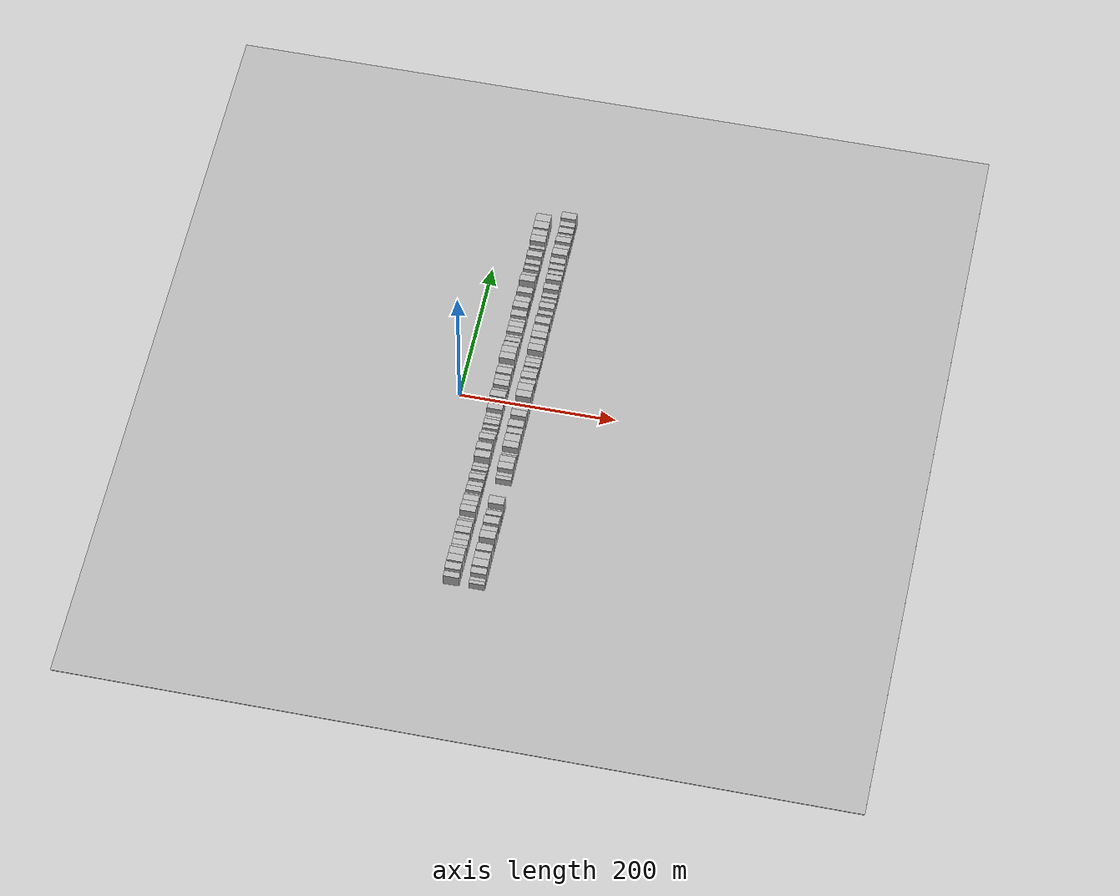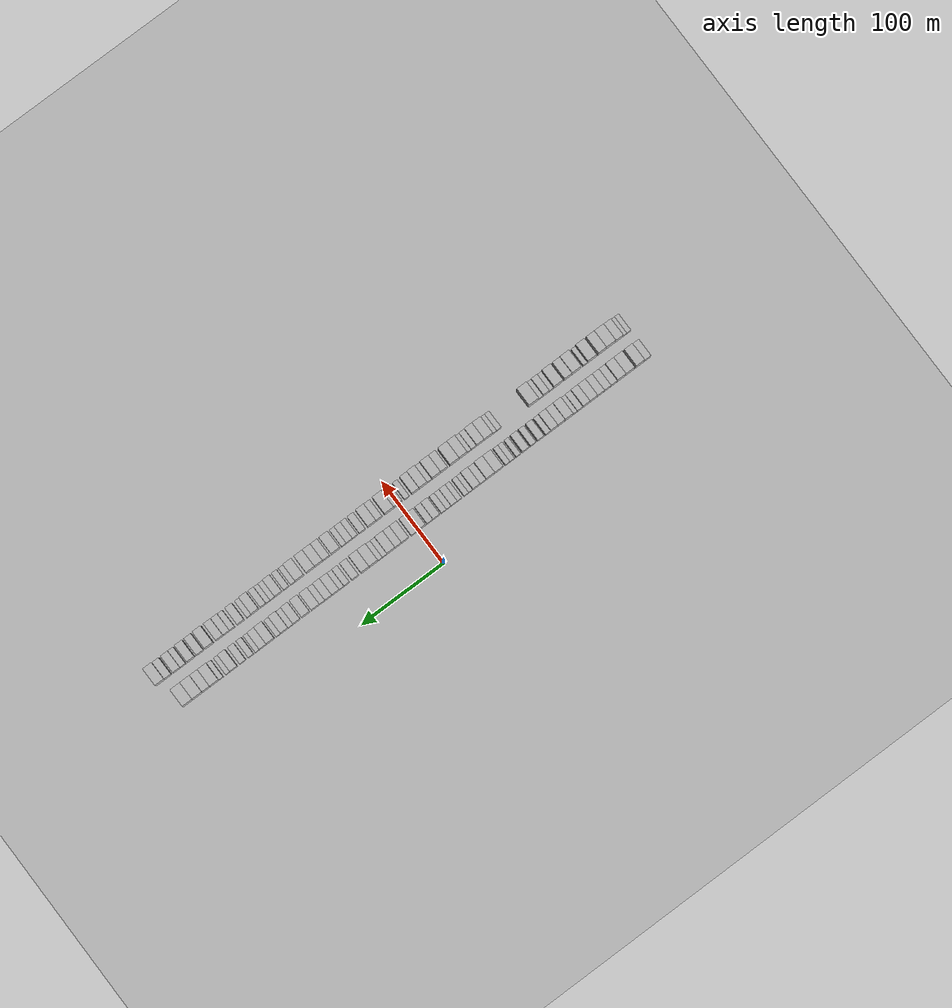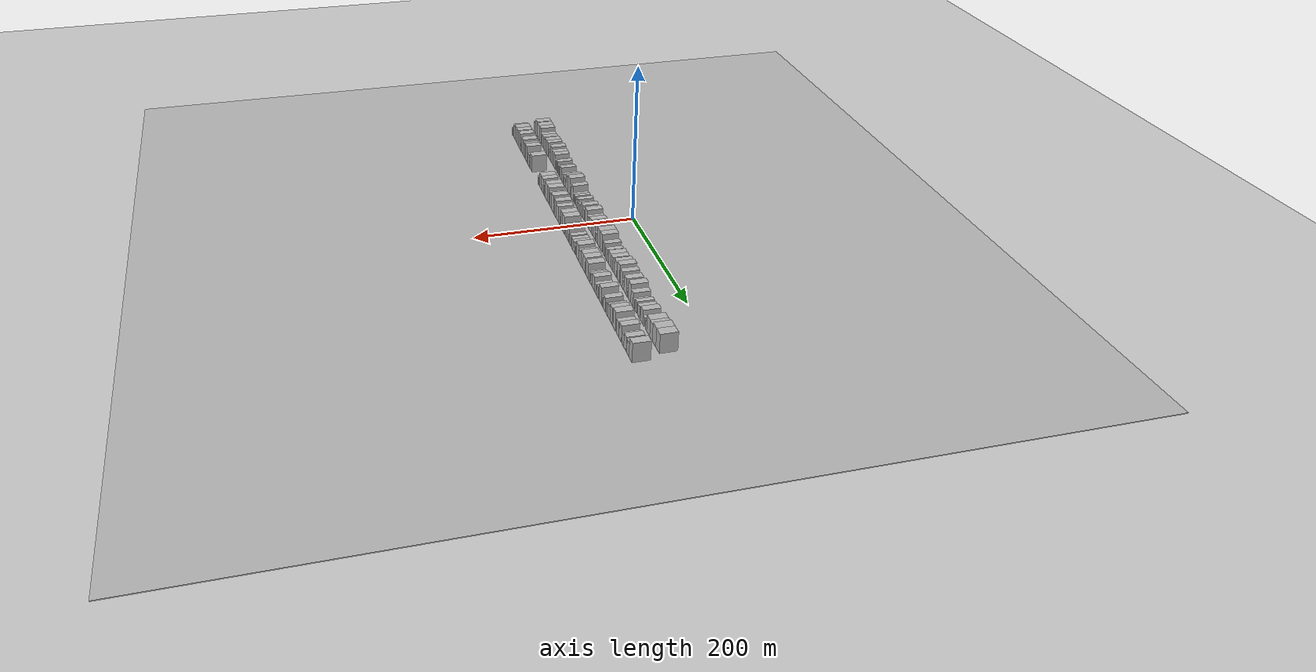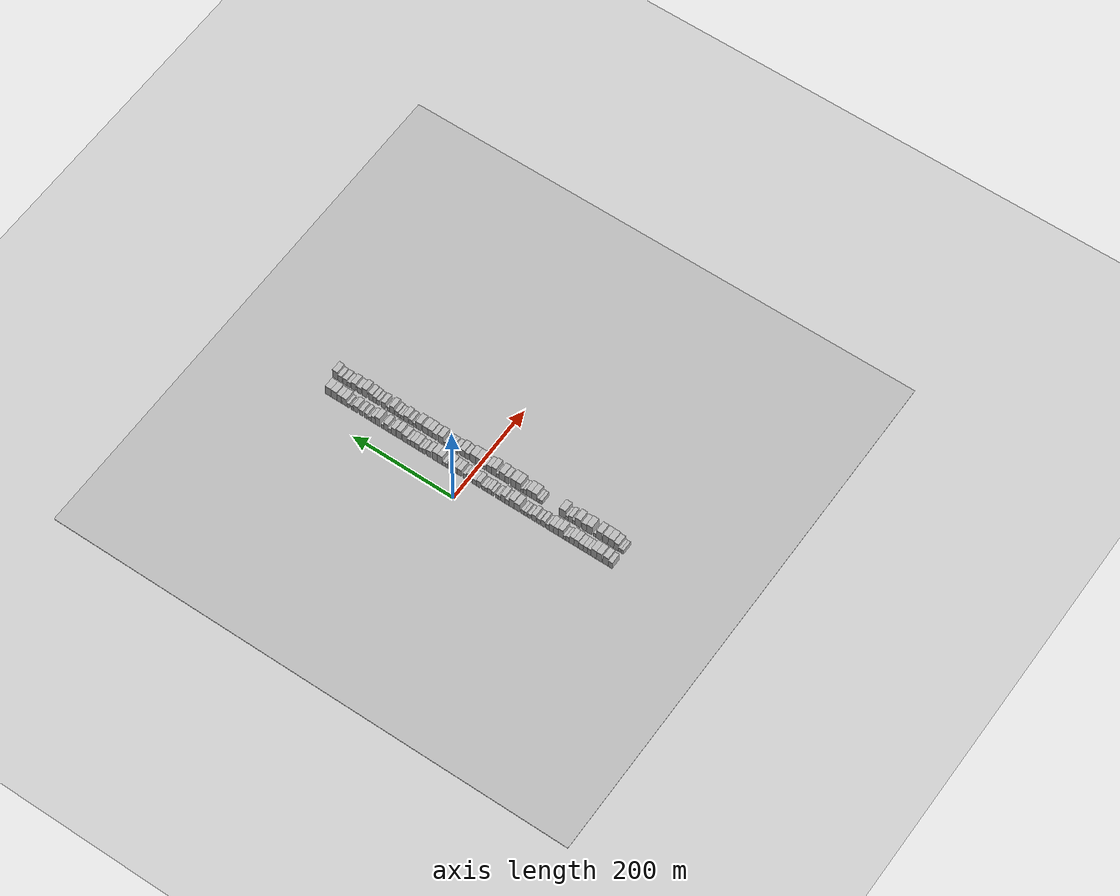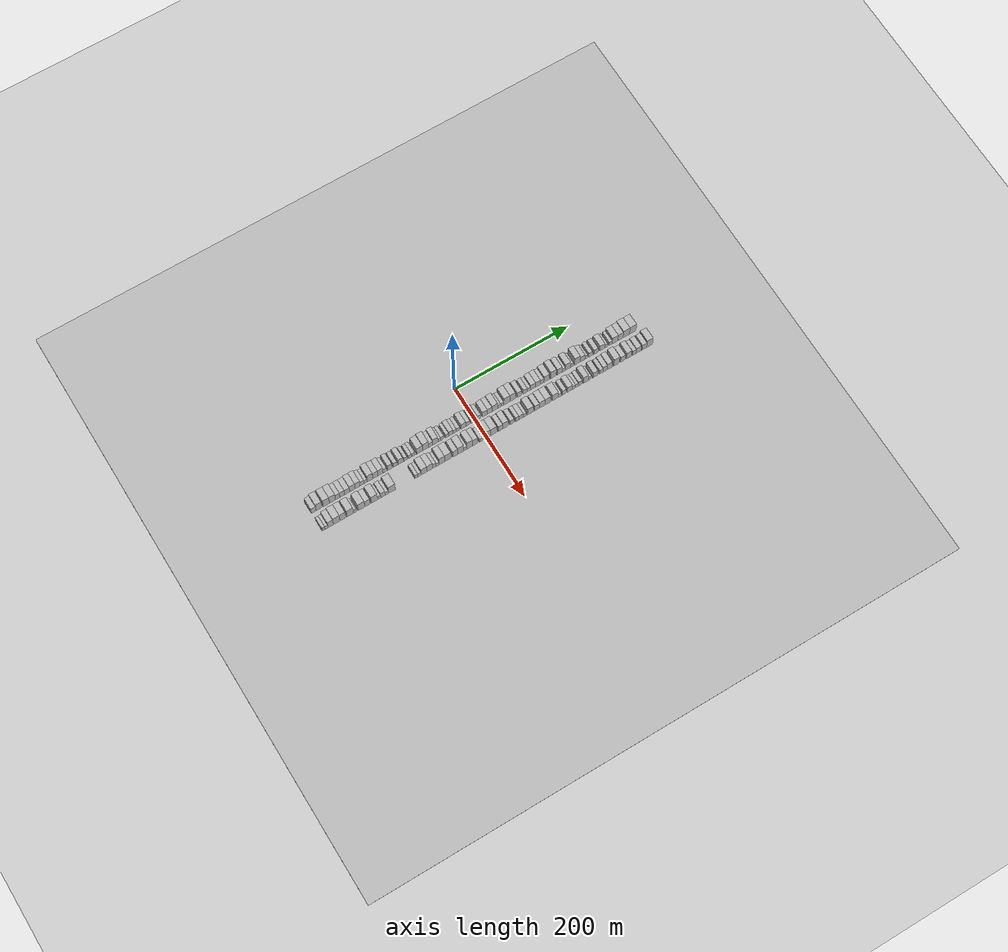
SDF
<?xml version="1.0" encoding="utf-8"?>

<sdf version="1.6">

   <world name="default">

      <gui fullscreen="0">

         <camera name="user_camera">

            <pose>-15 0 4.57585 0 0 0</pose>

            <view_controller>orbit</view_controller>

         </camera>

      </gui>

      <scene>

         <sky>

           <clouds>

             <speed>12</speed>

           </clouds>

         </sky>

         <ambient>0.4 0.4 0.4 1</ambient>

         <background>0.7 0.7 0.7 1</background>

         <shadows>1</shadows>

      </scene>

      <gravity>0 0 -9.8066</gravity>

      <magnetic_field>6e-06 2.3e-05 -4.2e-05</magnetic_field>

      <physics default="0" name="default_physics" type="ode">

         <ode>

            <solver>

               <type>quick</type>

               <iters>10</iters>

               <sor>1.0</sor>

               <use_dynamic_moi_rescaling>0</use_dynamic_moi_rescaling>

            </solver>

            <constraints>

               <cfm>0</cfm>

               <erp>0.2</erp>

               <contact_max_correcting_vel>100</contact_max_correcting_vel>

               <contact_surface_layer>0.001</contact_surface_layer>

            </constraints>

         </ode>

         <max_step_size>0.004</max_step_size>

         <real_time_factor>1</real_time_factor>

         <real_time_update_rate>250</real_time_update_rate>

      </physics>

      <light name="sun" type="directional">

         <cast_shadows>1</cast_shadows>

         <pose>0 0 10 0 0 0</pose>

         <diffuse>0.8 0.8 0.8 1</diffuse>

         <specular>0.2 0.2 0.2 1</specular>

         <attenuation>

            <range>1000</range>

            <constant>0.9</constant>

            <linear>0.01</linear>

            <quadratic>0.001</quadratic>

         </attenuation>

         <direction>-0.5 0.1 -0.9</direction>

      </light>

      <include>

         <name>ground_plane_1</name>

         <uri>model://HANNAS_ground_plane</uri>

         <pose>0 0 0  0 0 0</pose>

      </include>

      <include>

         <name>ground_plane_2</name>

         <uri>model://HANNAS_ground_plane</uri>

         <pose>100 0 0  0 0 0</pose>

      </include>

      <model name="building_1">

         <static>1</static>

         <pose frame="">50.0000 -277.9557 0 0.000000 0.000000 0.000000</pose>

         <link name="link">

            <pose frame="">0 0 9.00 0 0 0</pose>

            <collision name="collision">

               <geometry>

                  <box>

                     <size>20.0000 8.0885 18.0000</size>

                  </box>

               </geometry>

               <max_contacts>10</max_contacts>

               <surface>

                  <contact>

                     <ode/>

                  </contact>

                  <bounce/>

                  <friction>

                     <torsional>

                        <ode/>

                     </torsional>

                     <ode/>

                  </friction>

               </surface>

            </collision>

            <visual name="visual">

               <cast_shadows>0</cast_shadows>

               <geometry>

                  <box>

                     <size>20.0000 8.0885 18.0000</size>

                  </box>

               </geometry>

               <material>

                  <script>

                     <uri>model://HANNAS_wall/materials/scripts</uri>

                     <uri>model://HANNAS_wall/materials/textures</uri>

                     <name>vrc/HANNAS_wall</name>

                  </script>

               </material>

            </visual>

            <self_collide>0</self_collide>

            <enable_wind>0</enable_wind>

            <kinematic>0</kinematic>

         </link>

      </model>

      <model name="building_2">

         <static>1</static>

         <pose frame="">50.0000 -268.8306 0 0.000000 0.000000 0.000000</pose>

         <link name="link">

            <pose frame="">0 0 12.00 0 0 0</pose>

            <collision name="collision">

               <geometry>

                  <box>

                     <size>20.0000 10.1618 24.0000</size>

                  </box>

               </geometry>

               <max_contacts>10</max_contacts>

               <surface>

                  <contact>

                     <ode/>

                  </contact>

                  <bounce/>

                  <friction>

                     <torsional>

                        <ode/>

                     </torsional>

                     <ode/>

                  </friction>

               </surface>

            </collision>

            <visual name="visual">

               <cast_shadows>0</cast_shadows>

               <geometry>

                  <box>

                     <size>20.0000 10.1618 24.0000</size>

                  </box>

               </geometry>

               <material>

                  <script>

                     <uri>model://HANNAS_wall/materials/scripts</uri>

                     <uri>model://HANNAS_wall/materials/textures</uri>

                     <name>vrc/HANNAS_wall</name>

                  </script>

               </material>

            </visual>

            <self_collide>0</self_collide>

            <enable_wind>0</enable_wind>

            <kinematic>0</kinematic>

         </link>

      </model>

      <model name="building_3">

         <static>1</static>

         <pose frame="">50.0000 -256.4384 0 0.000000 0.000000 0.000000</pose>

         <link name="link">

            <pose frame="">0 0 12.00 0 0 0</pose>

            <collision name="collision">

               <geometry>

                  <box>

                     <size>20.0000 10.6225 24.0000</size>

                  </box>

               </geometry>

               <max_contacts>10</max_contacts>

               <surface>

                  <contact>

                     <ode/>

                  </contact>

                  <bounce/>

                  <friction>

                     <torsional>

                        <ode/>

                     </torsional>

                     <ode/>

                  </friction>

               </surface>

            </collision>

            <visual name="visual">

               <cast_shadows>0</cast_shadows>

               <geometry>

                  <box>

                     <size>20.0000 10.6225 24.0000</size>

                  </box>

               </geometry>

               <material>

                  <script>

                     <uri>model://HANNAS_wall/materials/scripts</uri>

                     <uri>model://HANNAS_wall/materials/textures</uri>

                     <name>vrc/HANNAS_wall</name>

                  </script>

               </material>

            </visual>

            <self_collide>0</self_collide>

            <enable_wind>0</enable_wind>

            <kinematic>0</kinematic>

         </link>

      </model>

      <model name="building_4">

         <static>1</static>

         <pose frame="">50.0000 -246.0642 0 0.000000 0.000000 0.000000</pose>

         <link name="link">

            <pose frame="">0 0 12.00 0 0 0</pose>

            <collision name="collision">

               <geometry>

                  <box>

                     <size>20.0000 10.1259 24.0000</size>

                  </box>

               </geometry>

               <max_contacts>10</max_contacts>

               <surface>

                  <contact>

                     <ode/>

                  </contact>

                  <bounce/>

                  <friction>

                     <torsional>

                        <ode/>

                     </torsional>

                     <ode/>

                  </friction>

               </surface>

            </collision>

            <visual name="visual">

               <cast_shadows>0</cast_shadows>

               <geometry>

                  <box>

                     <size>20.0000 10.1259 24.0000</size>

                  </box>

               </geometry>

               <material>

                  <script>

                     <uri>model://HANNAS_wall/materials/scripts</uri>

                     <uri>model://HANNAS_wall/materials/textures</uri>

                     <name>vrc/HANNAS_wall</name>

                  </script>

               </material>

            </visual>

            <self_collide>0</self_collide>

            <enable_wind>0</enable_wind>

            <kinematic>0</kinematic>

         </link>

      </model>

      <model name="building_5">

         <static>1</static>

         <pose frame="">50.0000 -237.2172 0 0.000000 0.000000 0.000000</pose>

         <link name="link">

            <pose frame="">0 0 9.00 0 0 0</pose>

            <collision name="collision">

               <geometry>

                  <box>

                     <size>20.0000 7.5681 18.0000</size>

                  </box>

               </geometry>

               <max_contacts>10</max_contacts>

               <surface>

                  <contact>

                     <ode/>

                  </contact>

                  <bounce/>

                  <friction>

                     <torsional>

                        <ode/>

                     </torsional>

                     <ode/>

                  </friction>

               </surface>

            </collision>

            <visual name="visual">

               <cast_shadows>0</cast_shadows>

               <geometry>

                  <box>

                     <size>20.0000 7.5681 18.0000</size>

                  </box>

               </geometry>

               <material>

                  <script>

                     <uri>model://HANNAS_wall/materials/scripts</uri>

                     <uri>model://HANNAS_wall/materials/textures</uri>

                     <name>vrc/HANNAS_wall</name>

                  </script>

               </material>

            </visual>

            <self_collide>0</self_collide>

            <enable_wind>0</enable_wind>

            <kinematic>0</kinematic>

         </link>

      </model>

      <model name="building_6">

         <static>1</static>

         <pose frame="">50.0000 -229.4147 0 0.000000 0.000000 0.000000</pose>

         <link name="link">

            <pose frame="">0 0 9.00 0 0 0</pose>

            <collision name="collision">

               <geometry>

                  <box>

                     <size>20.0000 8.0370 18.0000</size>

                  </box>

               </geometry>

               <max_contacts>10</max_contacts>

               <surface>

                  <contact>

                     <ode/>

                  </contact>

                  <bounce/>

                  <friction>

                     <torsional>

                        <ode/>

                     </torsional>

                     <ode/>

                  </friction>

               </surface>

            </collision>

            <visual name="visual">

               <cast_shadows>0</cast_shadows>

               <geometry>

                  <box>

                     <size>20.0000 8.0370 18.0000</size>

                  </box>

               </geometry>

               <material>

                  <script>

                     <uri>model://HANNAS_wall/materials/scripts</uri>

                     <uri>model://HANNAS_wall/materials/textures</uri>

                     <name>vrc/HANNAS_wall</name>

                  </script>

               </material>

            </visual>

            <self_collide>0</self_collide>

            <enable_wind>0</enable_wind>

            <kinematic>0</kinematic>

         </link>

      </model>

      <model name="building_7">

         <static>1</static>

         <pose frame="">50.0000 -221.1382 0 0.000000 0.000000 0.000000</pose>

         <link name="link">

            <pose frame="">0 0 9.00 0 0 0</pose>

            <collision name="collision">

               <geometry>

                  <box>

                     <size>20.0000 8.5159 18.0000</size>

                  </box>

               </geometry>

               <max_contacts>10</max_contacts>

               <surface>

                  <contact>

                     <ode/>

                  </contact>

                  <bounce/>

                  <friction>

                     <torsional>

                        <ode/>

                     </torsional>

                     <ode/>

                  </friction>

               </surface>

            </collision>

            <visual name="visual">

               <cast_shadows>0</cast_shadows>

               <geometry>

                  <box>

                     <size>20.0000 8.5159 18.0000</size>

                  </box>

               </geometry>

               <material>

                  <script>

                     <uri>model://HANNAS_wall/materials/scripts</uri>

                     <uri>model://HANNAS_wall/materials/textures</uri>

                     <name>vrc/HANNAS_wall</name>

                  </script>

               </material>

            </visual>

            <self_collide>0</self_collide>

            <enable_wind>0</enable_wind>

            <kinematic>0</kinematic>

         </link>

      </model>

      <model name="building_8">

         <static>1</static>

         <pose frame="">50.0000 -212.2553 0 0.000000 0.000000 0.000000</pose>

         <link name="link">

            <pose frame="">0 0 10.50 0 0 0</pose>

            <collision name="collision">

               <geometry>

                  <box>

                     <size>20.0000 9.2499 21.0000</size>

                  </box>

               </geometry>

               <max_contacts>10</max_contacts>

               <surface>

                  <contact>

                     <ode/>

                  </contact>

                  <bounce/>

                  <friction>

                     <torsional>

                        <ode/>

                     </torsional>

                     <ode/>

                  </friction>

               </surface>

            </collision>

            <visual name="visual">

               <cast_shadows>0</cast_shadows>

               <geometry>

                  <box>

                     <size>20.0000 9.2499 21.0000</size>

                  </box>

               </geometry>

               <material>

                  <script>

                     <uri>model://HANNAS_wall/materials/scripts</uri>

                     <uri>model://HANNAS_wall/materials/textures</uri>

                     <name>vrc/HANNAS_wall</name>

                  </script>

               </material>

            </visual>

            <self_collide>0</self_collide>

            <enable_wind>0</enable_wind>

            <kinematic>0</kinematic>

         </link>

      </model>

      <model name="building_9">

         <static>1</static>

         <pose frame="">50.0000 -203.4296 0 0.000000 0.000000 0.000000</pose>

         <link name="link">

            <pose frame="">0 0 10.50 0 0 0</pose>

            <collision name="collision">

               <geometry>

                  <box>

                     <size>20.0000 8.4014 21.0000</size>

                  </box>

               </geometry>

               <max_contacts>10</max_contacts>

               <surface>

                  <contact>

                     <ode/>

                  </contact>

                  <bounce/>

                  <friction>

                     <torsional>

                        <ode/>

                     </torsional>

                     <ode/>

                  </friction>

               </surface>

            </collision>

            <visual name="visual">

               <cast_shadows>0</cast_shadows>

               <geometry>

                  <box>

                     <size>20.0000 8.4014 21.0000</size>

                  </box>

               </geometry>

               <material>

                  <script>

                     <uri>model://HANNAS_wall/materials/scripts</uri>

                     <uri>model://HANNAS_wall/materials/textures</uri>

                     <name>vrc/HANNAS_wall</name>

                  </script>

               </material>

            </visual>

            <self_collide>0</self_collide>

            <enable_wind>0</enable_wind>

            <kinematic>0</kinematic>

         </link>

      </model>

      <model name="building_10">

         <static>1</static>

         <pose frame="">50.0000 -195.8593 0 0.000000 0.000000 0.000000</pose>

         <link name="link">

            <pose frame="">0 0 7.50 0 0 0</pose>

            <collision name="collision">

               <geometry>

                  <box>

                     <size>20.0000 6.7391 15.0000</size>

                  </box>

               </geometry>

               <max_contacts>10</max_contacts>

               <surface>

                  <contact>

                     <ode/>

                  </contact>

                  <bounce/>

                  <friction>

                     <torsional>

                        <ode/>

                     </torsional>

                     <ode/>

                  </friction>

               </surface>

            </collision>

            <visual name="visual">

               <cast_shadows>0</cast_shadows>

               <geometry>

                  <box>

                     <size>20.0000 6.7391 15.0000</size>

                  </box>

               </geometry>

               <material>

                  <script>

                     <uri>model://HANNAS_wall/materials/scripts</uri>

                     <uri>model://HANNAS_wall/materials/textures</uri>

                     <name>vrc/HANNAS_wall</name>

                  </script>

               </material>

            </visual>

            <self_collide>0</self_collide>

            <enable_wind>0</enable_wind>

            <kinematic>0</kinematic>

         </link>

      </model>

      <model name="building_11">

         <static>1</static>

         <pose frame="">50.0000 -189.7032 0 0.000000 0.000000 0.000000</pose>

         <link name="link">

            <pose frame="">0 0 6.00 0 0 0</pose>

            <collision name="collision">

               <geometry>

                  <box>

                     <size>20.0000 5.5732 12.0000</size>

                  </box>

               </geometry>

               <max_contacts>10</max_contacts>

               <surface>

                  <contact>

                     <ode/>

                  </contact>

                  <bounce/>

                  <friction>

                     <torsional>

                        <ode/>

                     </torsional>

                     <ode/>

                  </friction>

               </surface>

            </collision>

            <visual name="visual">

               <cast_shadows>0</cast_shadows>

               <geometry>

                  <box>

                     <size>20.0000 5.5732 12.0000</size>

                  </box>

               </geometry>

               <material>

                  <script>

                     <uri>model://HANNAS_wall/materials/scripts</uri>

                     <uri>model://HANNAS_wall/materials/textures</uri>

                     <name>vrc/HANNAS_wall</name>

                  </script>

               </material>

            </visual>

            <self_collide>0</self_collide>

            <enable_wind>0</enable_wind>

            <kinematic>0</kinematic>

         </link>

      </model>

      <model name="building_12">

         <static>1</static>

         <pose frame="">50.0000 -182.1112 0 0.000000 0.000000 0.000000</pose>

         <link name="link">

            <pose frame="">0 0 12.00 0 0 0</pose>

            <collision name="collision">

               <geometry>

                  <box>

                     <size>20.0000 9.6108 24.0000</size>

                  </box>

               </geometry>

               <max_contacts>10</max_contacts>

               <surface>

                  <contact>

                     <ode/>

                  </contact>

                  <bounce/>

                  <friction>

                     <torsional>

                        <ode/>

                     </torsional>

                     <ode/>

                  </friction>

               </surface>

            </collision>

            <visual name="visual">

               <cast_shadows>0</cast_shadows>

               <geometry>

                  <box>

                     <size>20.0000 9.6108 24.0000</size>

                  </box>

               </geometry>

               <material>

                  <script>

                     <uri>model://HANNAS_wall/materials/scripts</uri>

                     <uri>model://HANNAS_wall/materials/textures</uri>

                     <name>vrc/HANNAS_wall</name>

                  </script>

               </material>

            </visual>

            <self_collide>0</self_collide>

            <enable_wind>0</enable_wind>

            <kinematic>0</kinematic>

         </link>

      </model>

      <model name="building_13">

         <static>1</static>

         <pose frame="">50.0000 -172.9415 0 0.000000 0.000000 0.000000</pose>

         <link name="link">

            <pose frame="">0 0 10.50 0 0 0</pose>

            <collision name="collision">

               <geometry>

                  <box>

                     <size>20.0000 8.7288 21.0000</size>

                  </box>

               </geometry>

               <max_contacts>10</max_contacts>

               <surface>

                  <contact>

                     <ode/>

                  </contact>

                  <bounce/>

                  <friction>

                     <torsional>

                        <ode/>

                     </torsional>

                     <ode/>

                  </friction>

               </surface>

            </collision>

            <visual name="visual">

               <cast_shadows>0</cast_shadows>

               <geometry>

                  <box>

                     <size>20.0000 8.7288 21.0000</size>

                  </box>

               </geometry>

               <material>

                  <script>

                     <uri>model://HANNAS_wall/materials/scripts</uri>

                     <uri>model://HANNAS_wall/materials/textures</uri>

                     <name>vrc/HANNAS_wall</name>

                  </script>

               </material>

            </visual>

            <self_collide>0</self_collide>

            <enable_wind>0</enable_wind>

            <kinematic>0</kinematic>

         </link>

      </model>

      <model name="building_14">

         <static>1</static>

         <pose frame="">50.0000 -164.2269 0 0.000000 0.000000 0.000000</pose>

         <link name="link">

            <pose frame="">0 0 10.50 0 0 0</pose>

            <collision name="collision">

               <geometry>

                  <box>

                     <size>20.0000 8.7003 21.0000</size>

                  </box>

               </geometry>

               <max_contacts>10</max_contacts>

               <surface>

                  <contact>

                     <ode/>

                  </contact>

                  <bounce/>

                  <friction>

                     <torsional>

                        <ode/>

                     </torsional>

                     <ode/>

                  </friction>

               </surface>

            </collision>

            <visual name="visual">

               <cast_shadows>0</cast_shadows>

               <geometry>

                  <box>

                     <size>20.0000 8.7003 21.0000</size>

                  </box>

               </geometry>

               <material>

                  <script>

                     <uri>model://HANNAS_wall/materials/scripts</uri>

                     <uri>model://HANNAS_wall/materials/textures</uri>

                     <name>vrc/HANNAS_wall</name>

                  </script>

               </material>

            </visual>

            <self_collide>0</self_collide>

            <enable_wind>0</enable_wind>

            <kinematic>0</kinematic>

         </link>

      </model>

      <model name="building_15">

         <static>1</static>

         <pose frame="">50.0000 -156.8764 0 0.000000 0.000000 0.000000</pose>

         <link name="link">

            <pose frame="">0 0 7.50 0 0 0</pose>

            <collision name="collision">

               <geometry>

                  <box>

                     <size>20.0000 6.0009 15.0000</size>

                  </box>

               </geometry>

               <max_contacts>10</max_contacts>

               <surface>

                  <contact>

                     <ode/>

                  </contact>

                  <bounce/>

                  <friction>

                     <torsional>

                        <ode/>

                     </torsional>

                     <ode/>

                  </friction>

               </surface>

            </collision>

            <visual name="visual">

               <cast_shadows>0</cast_shadows>

               <geometry>

                  <box>

                     <size>20.0000 6.0009 15.0000</size>

                  </box>

               </geometry>

               <material>

                  <script>

                     <uri>model://HANNAS_wall/materials/scripts</uri>

                     <uri>model://HANNAS_wall/materials/textures</uri>

                     <name>vrc/HANNAS_wall</name>

                  </script>

               </material>

            </visual>

            <self_collide>0</self_collide>

            <enable_wind>0</enable_wind>

            <kinematic>0</kinematic>

         </link>

      </model>

      <model name="building_16">

         <static>1</static>

         <pose frame="">50.0000 -148.0398 0 0.000000 0.000000 0.000000</pose>

         <link name="link">

            <pose frame="">0 0 9.00 0 0 0</pose>

            <collision name="collision">

               <geometry>

                  <box>

                     <size>20.0000 7.6723 18.0000</size>

                  </box>

               </geometry>

               <max_contacts>10</max_contacts>

               <surface>

                  <contact>

                     <ode/>

                  </contact>

                  <bounce/>

                  <friction>

                     <torsional>

                        <ode/>

                     </torsional>

                     <ode/>

                  </friction>

               </surface>

            </collision>

            <visual name="visual">

               <cast_shadows>0</cast_shadows>

               <geometry>

                  <box>

                     <size>20.0000 7.6723 18.0000</size>

                  </box>

               </geometry>

               <material>

                  <script>

                     <uri>model://HANNAS_wall/materials/scripts</uri>

                     <uri>model://HANNAS_wall/materials/textures</uri>

                     <name>vrc/HANNAS_wall</name>

                  </script>

               </material>

            </visual>

            <self_collide>0</self_collide>

            <enable_wind>0</enable_wind>

            <kinematic>0</kinematic>

         </link>

      </model>

      <model name="building_17">

         <static>1</static>

         <pose frame="">50.0000 -138.9311 0 0.000000 0.000000 0.000000</pose>

         <link name="link">

            <pose frame="">0 0 7.50 0 0 0</pose>

            <collision name="collision">

               <geometry>

                  <box>

                     <size>20.0000 6.5452 15.0000</size>

                  </box>

               </geometry>

               <max_contacts>10</max_contacts>

               <surface>

                  <contact>

                     <ode/>

                  </contact>

                  <bounce/>

                  <friction>

                     <torsional>

                        <ode/>

                     </torsional>

                     <ode/>

                  </friction>

               </surface>

            </collision>

            <visual name="visual">

               <cast_shadows>0</cast_shadows>

               <geometry>

                  <box>

                     <size>20.0000 6.5452 15.0000</size>

                  </box>

               </geometry>

               <material>

                  <script>

                     <uri>model://HANNAS_wall/materials/scripts</uri>

                     <uri>model://HANNAS_wall/materials/textures</uri>

                     <name>vrc/HANNAS_wall</name>

                  </script>

               </material>

            </visual>

            <self_collide>0</self_collide>

            <enable_wind>0</enable_wind>

            <kinematic>0</kinematic>

         </link>

      </model>

      <model name="building_18">

         <static>1</static>

         <pose frame="">50.0000 -129.6286 0 0.000000 0.000000 0.000000</pose>

         <link name="link">

            <pose frame="">0 0 9.00 0 0 0</pose>

            <collision name="collision">

               <geometry>

                  <box>

                     <size>20.0000 8.0599 18.0000</size>

                  </box>

               </geometry>

               <max_contacts>10</max_contacts>

               <surface>

                  <contact>

                     <ode/>

                  </contact>

                  <bounce/>

                  <friction>

                     <torsional>

                        <ode/>

                     </torsional>

                     <ode/>

                  </friction>

               </surface>

            </collision>

            <visual name="visual">

               <cast_shadows>0</cast_shadows>

               <geometry>

                  <box>

                     <size>20.0000 8.0599 18.0000</size>

                  </box>

               </geometry>

               <material>

                  <script>

                     <uri>model://HANNAS_wall/materials/scripts</uri>

                     <uri>model://HANNAS_wall/materials/textures</uri>

                     <name>vrc/HANNAS_wall</name>

                  </script>

               </material>

            </visual>

            <self_collide>0</self_collide>

            <enable_wind>0</enable_wind>

            <kinematic>0</kinematic>

         </link>

      </model>

      <model name="building_19">

         <static>1</static>

         <pose frame="">50.0000 -120.9239 0 0.000000 0.000000 0.000000</pose>

         <link name="link">

            <pose frame="">0 0 6.00 0 0 0</pose>

            <collision name="collision">

               <geometry>

                  <box>

                     <size>20.0000 5.3495 12.0000</size>

                  </box>

               </geometry>

               <max_contacts>10</max_contacts>

               <surface>

                  <contact>

                     <ode/>

                  </contact>

                  <bounce/>

                  <friction>

                     <torsional>

                        <ode/>

                     </torsional>

                     <ode/>

                  </friction>

               </surface>

            </collision>

            <visual name="visual">

               <cast_shadows>0</cast_shadows>

               <geometry>

                  <box>

                     <size>20.0000 5.3495 12.0000</size>

                  </box>

               </geometry>

               <material>

                  <script>

                     <uri>model://HANNAS_wall/materials/scripts</uri>

                     <uri>model://HANNAS_wall/materials/textures</uri>

                     <name>vrc/HANNAS_wall</name>

                  </script>

               </material>

            </visual>

            <self_collide>0</self_collide>

            <enable_wind>0</enable_wind>

            <kinematic>0</kinematic>

         </link>

      </model>

      <model name="building_20">

         <static>1</static>

         <pose frame="">50.0000 -113.4339 0 0.000000 0.000000 0.000000</pose>

         <link name="link">

            <pose frame="">0 0 6.00 0 0 0</pose>

            <collision name="collision">

               <geometry>

                  <box>

                     <size>20.0000 5.6305 12.0000</size>

                  </box>

               </geometry>

               <max_contacts>10</max_contacts>

               <surface>

                  <contact>

                     <ode/>

                  </contact>

                  <bounce/>

                  <friction>

                     <torsional>

                        <ode/>

                     </torsional>

                     <ode/>

                  </friction>

               </surface>

            </collision>

            <visual name="visual">

               <cast_shadows>0</cast_shadows>

               <geometry>

                  <box>

                     <size>20.0000 5.6305 12.0000</size>

                  </box>

               </geometry>

               <material>

                  <script>

                     <uri>model://HANNAS_wall/materials/scripts</uri>

                     <uri>model://HANNAS_wall/materials/textures</uri>

                     <name>vrc/HANNAS_wall</name>

                  </script>

               </material>

            </visual>

            <self_collide>0</self_collide>

            <enable_wind>0</enable_wind>

            <kinematic>0</kinematic>

         </link>

      </model>

      <model name="building_21">

         <static>1</static>

         <pose frame="">50.0000 -107.8615 0 0.000000 0.000000 0.000000</pose>

         <link name="link">

            <pose frame="">0 0 6.00 0 0 0</pose>

            <collision name="collision">

               <geometry>

                  <box>

                     <size>20.0000 5.5142 12.0000</size>

                  </box>

               </geometry>

               <max_contacts>10</max_contacts>

               <surface>

                  <contact>

                     <ode/>

                  </contact>

                  <bounce/>

                  <friction>

                     <torsional>

                        <ode/>

                     </torsional>

                     <ode/>

                  </friction>

               </surface>

            </collision>

            <visual name="visual">

               <cast_shadows>0</cast_shadows>

               <geometry>

                  <box>

                     <size>20.0000 5.5142 12.0000</size>

                  </box>

               </geometry>

               <material>

                  <script>

                     <uri>model://HANNAS_wall/materials/scripts</uri>

                     <uri>model://HANNAS_wall/materials/textures</uri>

                     <name>vrc/HANNAS_wall</name>

                  </script>

               </material>

            </visual>

            <self_collide>0</self_collide>

            <enable_wind>0</enable_wind>

            <kinematic>0</kinematic>

         </link>

      </model>

      <model name="building_22">

         <static>1</static>

         <pose frame="">50.0000 -96.9569 0 0.000000 0.000000 0.000000</pose>

         <link name="link">

            <pose frame="">0 0 10.50 0 0 0</pose>

            <collision name="collision">

               <geometry>

                  <box>

                     <size>20.0000 10.2951 21.0000</size>

                  </box>

               </geometry>

               <max_contacts>10</max_contacts>

               <surface>

                  <contact>

                     <ode/>

                  </contact>

                  <bounce/>

                  <friction>

                     <torsional>

                        <ode/>

                     </torsional>

                     <ode/>

                  </friction>

               </surface>

            </collision>

            <visual name="visual">

               <cast_shadows>0</cast_shadows>

               <geometry>

                  <box>

                     <size>20.0000 10.2951 21.0000</size>

                  </box>

               </geometry>

               <material>

                  <script>

                     <uri>model://HANNAS_wall/materials/scripts</uri>

                     <uri>model://HANNAS_wall/materials/textures</uri>

                     <name>vrc/HANNAS_wall</name>

                  </script>

               </material>

            </visual>

            <self_collide>0</self_collide>

            <enable_wind>0</enable_wind>

            <kinematic>0</kinematic>

         </link>

      </model>

      <model name="building_23">

         <static>1</static>

         <pose frame="">50.0000 -86.6608 0 0.000000 0.000000 0.000000</pose>

         <link name="link">

            <pose frame="">0 0 12.00 0 0 0</pose>

            <collision name="collision">

               <geometry>

                  <box>

                     <size>20.0000 10.2970 24.0000</size>

                  </box>

               </geometry>

               <max_contacts>10</max_contacts>

               <surface>

                  <contact>

                     <ode/>

                  </contact>

                  <bounce/>

                  <friction>

                     <torsional>

                        <ode/>

                     </torsional>

                     <ode/>

                  </friction>

               </surface>

            </collision>

            <visual name="visual">

               <cast_shadows>0</cast_shadows>

               <geometry>

                  <box>

                     <size>20.0000 10.2970 24.0000</size>

                  </box>

               </geometry>

               <material>

                  <script>

                     <uri>model://HANNAS_wall/materials/scripts</uri>

                     <uri>model://HANNAS_wall/materials/textures</uri>

                     <name>vrc/HANNAS_wall</name>

                  </script>

               </material>

            </visual>

            <self_collide>0</self_collide>

            <enable_wind>0</enable_wind>

            <kinematic>0</kinematic>

         </link>

      </model>

      <model name="building_24">

         <static>1</static>

         <pose frame="">50.0000 -77.8001 0 0.000000 0.000000 0.000000</pose>

         <link name="link">

            <pose frame="">0 0 7.50 0 0 0</pose>

            <collision name="collision">

               <geometry>

                  <box>

                     <size>20.0000 7.4245 15.0000</size>

                  </box>

               </geometry>

               <max_contacts>10</max_contacts>

               <surface>

                  <contact>

                     <ode/>

                  </contact>

                  <bounce/>

                  <friction>

                     <torsional>

                        <ode/>

                     </torsional>

                     <ode/>

                  </friction>

               </surface>

            </collision>

            <visual name="visual">

               <cast_shadows>0</cast_shadows>

               <geometry>

                  <box>

                     <size>20.0000 7.4245 15.0000</size>

                  </box>

               </geometry>

               <material>

                  <script>

                     <uri>model://HANNAS_wall/materials/scripts</uri>

                     <uri>model://HANNAS_wall/materials/textures</uri>

                     <name>vrc/HANNAS_wall</name>

                  </script>

               </material>

            </visual>

            <self_collide>0</self_collide>

            <enable_wind>0</enable_wind>

            <kinematic>0</kinematic>

         </link>

      </model>

      <model name="building_25">

         <static>1</static>

         <pose frame="">50.0000 -69.6956 0 0.000000 0.000000 0.000000</pose>

         <link name="link">

            <pose frame="">0 0 10.50 0 0 0</pose>

            <collision name="collision">

               <geometry>

                  <box>

                     <size>20.0000 8.7845 21.0000</size>

                  </box>

               </geometry>

               <max_contacts>10</max_contacts>

               <surface>

                  <contact>

                     <ode/>

                  </contact>

                  <bounce/>

                  <friction>

                     <torsional>

                        <ode/>

                     </torsional>

                     <ode/>

                  </friction>

               </surface>

            </collision>

            <visual name="visual">

               <cast_shadows>0</cast_shadows>

               <geometry>

                  <box>

                     <size>20.0000 8.7845 21.0000</size>

                  </box>

               </geometry>

               <material>

                  <script>

                     <uri>model://HANNAS_wall/materials/scripts</uri>

                     <uri>model://HANNAS_wall/materials/textures</uri>

                     <name>vrc/HANNAS_wall</name>

                  </script>

               </material>

            </visual>

            <self_collide>0</self_collide>

            <enable_wind>0</enable_wind>

            <kinematic>0</kinematic>

         </link>

      </model>

      <model name="building_26">

         <static>1</static>

         <pose frame="">50.0000 -62.8585 0 0.000000 0.000000 0.000000</pose>

         <link name="link">

            <pose frame="">0 0 6.00 0 0 0</pose>

            <collision name="collision">

               <geometry>

                  <box>

                     <size>20.0000 4.8897 12.0000</size>

                  </box>

               </geometry>

               <max_contacts>10</max_contacts>

               <surface>

                  <contact>

                     <ode/>

                  </contact>

                  <bounce/>

                  <friction>

                     <torsional>

                        <ode/>

                     </torsional>

                     <ode/>

                  </friction>

               </surface>

            </collision>

            <visual name="visual">

               <cast_shadows>0</cast_shadows>

               <geometry>

                  <box>

                     <size>20.0000 4.8897 12.0000</size>

                  </box>

               </geometry>

               <material>

                  <script>

                     <uri>model://HANNAS_wall/materials/scripts</uri>

                     <uri>model://HANNAS_wall/materials/textures</uri>

                     <name>vrc/HANNAS_wall</name>

                  </script>

               </material>

            </visual>

            <self_collide>0</self_collide>

            <enable_wind>0</enable_wind>

            <kinematic>0</kinematic>

         </link>

      </model>

      <model name="building_27">

         <static>1</static>

         <pose frame="">50.0000 -57.6630 0 0.000000 0.000000 0.000000</pose>

         <link name="link">

            <pose frame="">0 0 6.00 0 0 0</pose>

            <collision name="collision">

               <geometry>

                  <box>

                     <size>20.0000 5.5013 12.0000</size>

                  </box>

               </geometry>

               <max_contacts>10</max_contacts>

               <surface>

                  <contact>

                     <ode/>

                  </contact>

                  <bounce/>

                  <friction>

                     <torsional>

                        <ode/>

                     </torsional>

                     <ode/>

                  </friction>

               </surface>

            </collision>

            <visual name="visual">

               <cast_shadows>0</cast_shadows>

               <geometry>

                  <box>

                     <size>20.0000 5.5013 12.0000</size>

                  </box>

               </geometry>

               <material>

                  <script>

                     <uri>model://HANNAS_wall/materials/scripts</uri>

                     <uri>model://HANNAS_wall/materials/textures</uri>

                     <name>vrc/HANNAS_wall</name>

                  </script>

               </material>

            </visual>

            <self_collide>0</self_collide>

            <enable_wind>0</enable_wind>

            <kinematic>0</kinematic>

         </link>

      </model>

      <model name="building_28">

         <static>1</static>

         <pose frame="">50.0000 -49.2499 0 0.000000 0.000000 0.000000</pose>

         <link name="link">

            <pose frame="">0 0 6.00 0 0 0</pose>

            <collision name="collision">

               <geometry>

                  <box>

                     <size>20.0000 5.3249 12.0000</size>

                  </box>

               </geometry>

               <max_contacts>10</max_contacts>

               <surface>

                  <contact>

                     <ode/>

                  </contact>

                  <bounce/>

                  <friction>

                     <torsional>

                        <ode/>

                     </torsional>

                     <ode/>

                  </friction>

               </surface>

            </collision>

            <visual name="visual">

               <cast_shadows>0</cast_shadows>

               <geometry>

                  <box>

                     <size>20.0000 5.3249 12.0000</size>

                  </box>

               </geometry>

               <material>

                  <script>

                     <uri>model://HANNAS_wall/materials/scripts</uri>

                     <uri>model://HANNAS_wall/materials/textures</uri>

                     <name>vrc/HANNAS_wall</name>

                  </script>

               </material>

            </visual>

            <self_collide>0</self_collide>

            <enable_wind>0</enable_wind>

            <kinematic>0</kinematic>

         </link>

      </model>

      <model name="building_29">

         <static>1</static>

         <pose frame="">50.0000 -42.8600 0 0.000000 0.000000 0.000000</pose>

         <link name="link">

            <pose frame="">0 0 7.50 0 0 0</pose>

            <collision name="collision">

               <geometry>

                  <box>

                     <size>20.0000 7.4549 15.0000</size>

                  </box>

               </geometry>

               <max_contacts>10</max_contacts>

               <surface>

                  <contact>

                     <ode/>

                  </contact>

                  <bounce/>

                  <friction>

                     <torsional>

                        <ode/>

                     </torsional>

                     <ode/>

                  </friction>

               </surface>

            </collision>

            <visual name="visual">

               <cast_shadows>0</cast_shadows>

               <geometry>

                  <box>

                     <size>20.0000 7.4549 15.0000</size>

                  </box>

               </geometry>

               <material>

                  <script>

                     <uri>model://HANNAS_wall/materials/scripts</uri>

                     <uri>model://HANNAS_wall/materials/textures</uri>

                     <name>vrc/HANNAS_wall</name>

                  </script>

               </material>

            </visual>

            <self_collide>0</self_collide>

            <enable_wind>0</enable_wind>

            <kinematic>0</kinematic>

         </link>

      </model>

      <model name="building_30">

         <static>1</static>

         <pose frame="">50.0000 -36.2315 0 0.000000 0.000000 0.000000</pose>

         <link name="link">

            <pose frame="">0 0 6.00 0 0 0</pose>

            <collision name="collision">

               <geometry>

                  <box>

                     <size>20.0000 5.8020 12.0000</size>

                  </box>

               </geometry>

               <max_contacts>10</max_contacts>

               <surface>

                  <contact>

                     <ode/>

                  </contact>

                  <bounce/>

                  <friction>

                     <torsional>

                        <ode/>

                     </torsional>

                     <ode/>

                  </friction>

               </surface>

            </collision>

            <visual name="visual">

               <cast_shadows>0</cast_shadows>

               <geometry>

                  <box>

                     <size>20.0000 5.8020 12.0000</size>

                  </box>

               </geometry>

               <material>

                  <script>

                     <uri>model://HANNAS_wall/materials/scripts</uri>

                     <uri>model://HANNAS_wall/materials/textures</uri>

                     <name>vrc/HANNAS_wall</name>

                  </script>

               </material>

            </visual>

            <self_collide>0</self_collide>

            <enable_wind>0</enable_wind>

            <kinematic>0</kinematic>

         </link>

      </model>

      <model name="building_31">

         <static>1</static>

         <pose frame="">50.0000 -30.3427 0 0.000000 0.000000 0.000000</pose>

         <link name="link">

            <pose frame="">0 0 6.00 0 0 0</pose>

            <collision name="collision">

               <geometry>

                  <box>

                     <size>20.0000 5.9757 12.0000</size>

                  </box>

               </geometry>

               <max_contacts>10</max_contacts>

               <surface>

                  <contact>

                     <ode/>

                  </contact>

                  <bounce/>

                  <friction>

                     <torsional>

                        <ode/>

                     </torsional>

                     <ode/>

                  </friction>

               </surface>

            </collision>

            <visual name="visual">

               <cast_shadows>0</cast_shadows>

               <geometry>

                  <box>

                     <size>20.0000 5.9757 12.0000</size>

                  </box>

               </geometry>

               <material>

                  <script>

                     <uri>model://HANNAS_wall/materials/scripts</uri>

                     <uri>model://HANNAS_wall/materials/textures</uri>

                     <name>vrc/HANNAS_wall</name>

                  </script>

               </material>

            </visual>

            <self_collide>0</self_collide>

            <enable_wind>0</enable_wind>

            <kinematic>0</kinematic>

         </link>

      </model>

      <model name="building_32">

         <static>1</static>

         <pose frame="">50.0000 -21.1666 0 0.000000 0.000000 0.000000</pose>

         <link name="link">

            <pose frame="">0 0 9.00 0 0 0</pose>

            <collision name="collision">

               <geometry>

                  <box>

                     <size>20.0000 8.3766 18.0000</size>

                  </box>

               </geometry>

               <max_contacts>10</max_contacts>

               <surface>

                  <contact>

                     <ode/>

                  </contact>

                  <bounce/>

                  <friction>

                     <torsional>

                        <ode/>

                     </torsional>

                     <ode/>

                  </friction>

               </surface>

            </collision>

            <visual name="visual">

               <cast_shadows>0</cast_shadows>

               <geometry>

                  <box>

                     <size>20.0000 8.3766 18.0000</size>

                  </box>

               </geometry>

               <material>

                  <script>

                     <uri>model://HANNAS_wall/materials/scripts</uri>

                     <uri>model://HANNAS_wall/materials/textures</uri>

                     <name>vrc/HANNAS_wall</name>

                  </script>

               </material>

            </visual>

            <self_collide>0</self_collide>

            <enable_wind>0</enable_wind>

            <kinematic>0</kinematic>

         </link>

      </model>

      <model name="building_33">

         <static>1</static>

         <pose frame="">50.0000 -13.4240 0 0.000000 0.000000 0.000000</pose>

         <link name="link">

            <pose frame="">0 0 7.50 0 0 0</pose>

            <collision name="collision">

               <geometry>

                  <box>

                     <size>20.0000 7.1086 15.0000</size>

                  </box>

               </geometry>

               <max_contacts>10</max_contacts>

               <surface>

                  <contact>

                     <ode/>

                  </contact>

                  <bounce/>

                  <friction>

                     <torsional>

                        <ode/>

                     </torsional>

                     <ode/>

                  </friction>

               </surface>

            </collision>

            <visual name="visual">

               <cast_shadows>0</cast_shadows>

               <geometry>

                  <box>

                     <size>20.0000 7.1086 15.0000</size>

                  </box>

               </geometry>

               <material>

                  <script>

                     <uri>model://HANNAS_wall/materials/scripts</uri>

                     <uri>model://HANNAS_wall/materials/textures</uri>

                     <name>vrc/HANNAS_wall</name>

                  </script>

               </material>

            </visual>

            <self_collide>0</self_collide>

            <enable_wind>0</enable_wind>

            <kinematic>0</kinematic>

         </link>

      </model>

      <model name="building_34">

         <static>1</static>

         <pose frame="">50.0000 -2.9296 0 0.000000 0.000000 0.000000</pose>

         <link name="link">

            <pose frame="">0 0 10.50 0 0 0</pose>

            <collision name="collision">

               <geometry>

                  <box>

                     <size>20.0000 9.8801 21.0000</size>

                  </box>

               </geometry>

               <max_contacts>10</max_contacts>

               <surface>

                  <contact>

                     <ode/>

                  </contact>

                  <bounce/>

                  <friction>

                     <torsional>

                        <ode/>

                     </torsional>

                     <ode/>

                  </friction>

               </surface>

            </collision>

            <visual name="visual">

               <cast_shadows>0</cast_shadows>

               <geometry>

                  <box>

                     <size>20.0000 9.8801 21.0000</size>

                  </box>

               </geometry>

               <material>

                  <script>

                     <uri>model://HANNAS_wall/materials/scripts</uri>

                     <uri>model://HANNAS_wall/materials/textures</uri>

                     <name>vrc/HANNAS_wall</name>

                  </script>

               </material>

            </visual>

            <self_collide>0</self_collide>

            <enable_wind>0</enable_wind>

            <kinematic>0</kinematic>

         </link>

      </model>

      <model name="building_35">

         <static>1</static>

         <pose frame="">50.0000 5.6101 0 0.000000 0.000000 0.000000</pose>

         <link name="link">

            <pose frame="">0 0 7.50 0 0 0</pose>

            <collision name="collision">

               <geometry>

                  <box>

                     <size>20.0000 7.1993 15.0000</size>

                  </box>

               </geometry>

               <max_contacts>10</max_contacts>

               <surface>

                  <contact>

                     <ode/>

                  </contact>

                  <bounce/>

                  <friction>

                     <torsional>

                        <ode/>

                     </torsional>

                     <ode/>

                  </friction>

               </surface>

            </collision>

            <visual name="visual">

               <cast_shadows>0</cast_shadows>

               <geometry>

                  <box>

                     <size>20.0000 7.1993 15.0000</size>

                  </box>

               </geometry>

               <material>

                  <script>

                     <uri>model://HANNAS_wall/materials/scripts</uri>

                     <uri>model://HANNAS_wall/materials/textures</uri>

                     <name>vrc/HANNAS_wall</name>

                  </script>

               </material>

            </visual>

            <self_collide>0</self_collide>

            <enable_wind>0</enable_wind>

            <kinematic>0</kinematic>

         </link>

      </model>

      <model name="building_36">

         <static>1</static>

         <pose frame="">50.0000 16.6000 0 0.000000 0.000000 0.000000</pose>

         <link name="link">

            <pose frame="">0 0 9.00 0 0 0</pose>

            <collision name="collision">

               <geometry>

                  <box>

                     <size>20.0000 8.7805 18.0000</size>

                  </box>

               </geometry>

               <max_contacts>10</max_contacts>

               <surface>

                  <contact>

                     <ode/>

                  </contact>

                  <bounce/>

                  <friction>

                     <torsional>

                        <ode/>

                     </torsional>

                     <ode/>

                  </friction>

               </surface>

            </collision>

            <visual name="visual">

               <cast_shadows>0</cast_shadows>

               <geometry>

                  <box>

                     <size>20.0000 8.7805 18.0000</size>

                  </box>

               </geometry>

               <material>

                  <script>

                     <uri>model://HANNAS_wall/materials/scripts</uri>

                     <uri>model://HANNAS_wall/materials/textures</uri>

                     <name>vrc/HANNAS_wall</name>

                  </script>

               </material>

            </visual>

            <self_collide>0</self_collide>

            <enable_wind>0</enable_wind>

            <kinematic>0</kinematic>

         </link>

      </model>

      <model name="building_37">

         <static>1</static>

         <pose frame="">50.0000 24.9277 0 0.000000 0.000000 0.000000</pose>

         <link name="link">

            <pose frame="">0 0 9.00 0 0 0</pose>

            <collision name="collision">

               <geometry>

                  <box>

                     <size>20.0000 7.8750 18.0000</size>

                  </box>

               </geometry>

               <max_contacts>10</max_contacts>

               <surface>

                  <contact>

                     <ode/>

                  </contact>

                  <bounce/>

                  <friction>

                     <torsional>

                        <ode/>

                     </torsional>

                     <ode/>

                  </friction>

               </surface>

            </collision>

            <visual name="visual">

               <cast_shadows>0</cast_shadows>

               <geometry>

                  <box>

                     <size>20.0000 7.8750 18.0000</size>

                  </box>

               </geometry>

               <material>

                  <script>

                     <uri>model://HANNAS_wall/materials/scripts</uri>

                     <uri>model://HANNAS_wall/materials/textures</uri>

                     <name>vrc/HANNAS_wall</name>

                  </script>

               </material>

            </visual>

            <self_collide>0</self_collide>

            <enable_wind>0</enable_wind>

            <kinematic>0</kinematic>

         </link>

      </model>

      <model name="building_38">

         <static>1</static>

         <pose frame="">50.0000 33.7858 0 0.000000 0.000000 0.000000</pose>

         <link name="link">

            <pose frame="">0 0 10.50 0 0 0</pose>

            <collision name="collision">

               <geometry>

                  <box>

                     <size>20.0000 9.8412 21.0000</size>

                  </box>

               </geometry>

               <max_contacts>10</max_contacts>

               <surface>

                  <contact>

                     <ode/>

                  </contact>

                  <bounce/>

                  <friction>

                     <torsional>

                        <ode/>

                     </torsional>

                     <ode/>

                  </friction>

               </surface>

            </collision>

            <visual name="visual">

               <cast_shadows>0</cast_shadows>

               <geometry>

                  <box>

                     <size>20.0000 9.8412 21.0000</size>

                  </box>

               </geometry>

               <material>

                  <script>

                     <uri>model://HANNAS_wall/materials/scripts</uri>

                     <uri>model://HANNAS_wall/materials/textures</uri>

                     <name>vrc/HANNAS_wall</name>

                  </script>

               </material>

            </visual>

            <self_collide>0</self_collide>

            <enable_wind>0</enable_wind>

            <kinematic>0</kinematic>

         </link>

      </model>

      <model name="building_39">

         <static>1</static>

         <pose frame="">50.0000 41.4476 0 0.000000 0.000000 0.000000</pose>

         <link name="link">

            <pose frame="">0 0 6.00 0 0 0</pose>

            <collision name="collision">

               <geometry>

                  <box>

                     <size>20.0000 5.4823 12.0000</size>

                  </box>

               </geometry>

               <max_contacts>10</max_contacts>

               <surface>

                  <contact>

                     <ode/>

                  </contact>

                  <bounce/>

                  <friction>

                     <torsional>

                        <ode/>

                     </torsional>

                     <ode/>

                  </friction>

               </surface>

            </collision>

            <visual name="visual">

               <cast_shadows>0</cast_shadows>

               <geometry>

                  <box>

                     <size>20.0000 5.4823 12.0000</size>

                  </box>

               </geometry>

               <material>

                  <script>

                     <uri>model://HANNAS_wall/materials/scripts</uri>

                     <uri>model://HANNAS_wall/materials/textures</uri>

                     <name>vrc/HANNAS_wall</name>

                  </script>

               </material>

            </visual>

            <self_collide>0</self_collide>

            <enable_wind>0</enable_wind>

            <kinematic>0</kinematic>

         </link>

      </model>

      <model name="building_40">

         <static>1</static>

         <pose frame="">50.0000 46.9185 0 0.000000 0.000000 0.000000</pose>

         <link name="link">

            <pose frame="">0 0 6.00 0 0 0</pose>

            <collision name="collision">

               <geometry>

                  <box>

                     <size>20.0000 5.4595 12.0000</size>

                  </box>

               </geometry>

               <max_contacts>10</max_contacts>

               <surface>

                  <contact>

                     <ode/>

                  </contact>

                  <bounce/>

                  <friction>

                     <torsional>

                        <ode/>

                     </torsional>

                     <ode/>

                  </friction>

               </surface>

            </collision>

            <visual name="visual">

               <cast_shadows>0</cast_shadows>

               <geometry>

                  <box>

                     <size>20.0000 5.4595 12.0000</size>

                  </box>

               </geometry>

               <material>

                  <script>

                     <uri>model://HANNAS_wall/materials/scripts</uri>

                     <uri>model://HANNAS_wall/materials/textures</uri>

                     <name>vrc/HANNAS_wall</name>

                  </script>

               </material>

            </visual>

            <self_collide>0</self_collide>

            <enable_wind>0</enable_wind>

            <kinematic>0</kinematic>

         </link>

      </model>

      <model name="building_41">

         <static>1</static>

         <pose frame="">50.0000 54.8365 0 0.000000 0.000000 0.000000</pose>

         <link name="link">

            <pose frame="">0 0 12.00 0 0 0</pose>

            <collision name="collision">

               <geometry>

                  <box>

                     <size>20.0000 10.3765 24.0000</size>

                  </box>

               </geometry>

               <max_contacts>10</max_contacts>

               <surface>

                  <contact>

                     <ode/>

                  </contact>

                  <bounce/>

                  <friction>

                     <torsional>

                        <ode/>

                     </torsional>

                     <ode/>

                  </friction>

               </surface>

            </collision>

            <visual name="visual">

               <cast_shadows>0</cast_shadows>

               <geometry>

                  <box>

                     <size>20.0000 10.3765 24.0000</size>

                  </box>

               </geometry>

               <material>

                  <script>

                     <uri>model://HANNAS_wall/materials/scripts</uri>

                     <uri>model://HANNAS_wall/materials/textures</uri>

                     <name>vrc/HANNAS_wall</name>

                  </script>

               </material>

            </visual>

            <self_collide>0</self_collide>

            <enable_wind>0</enable_wind>

            <kinematic>0</kinematic>

         </link>

      </model>

      <model name="building_42">

         <static>1</static>

         <pose frame="">50.0000 64.9680 0 0.000000 0.000000 0.000000</pose>

         <link name="link">

            <pose frame="">0 0 12.00 0 0 0</pose>

            <collision name="collision">

               <geometry>

                  <box>

                     <size>20.0000 9.8864 24.0000</size>

                  </box>

               </geometry>

               <max_contacts>10</max_contacts>

               <surface>

                  <contact>

                     <ode/>

                  </contact>

                  <bounce/>

                  <friction>

                     <torsional>

                        <ode/>

                     </torsional>

                     <ode/>

                  </friction>

               </surface>

            </collision>

            <visual name="visual">

               <cast_shadows>0</cast_shadows>

               <geometry>

                  <box>

                     <size>20.0000 9.8864 24.0000</size>

                  </box>

               </geometry>

               <material>

                  <script>

                     <uri>model://HANNAS_wall/materials/scripts</uri>

                     <uri>model://HANNAS_wall/materials/textures</uri>

                     <name>vrc/HANNAS_wall</name>

                  </script>

               </material>

            </visual>

            <self_collide>0</self_collide>

            <enable_wind>0</enable_wind>

            <kinematic>0</kinematic>

         </link>

      </model>

      <model name="building_43">

         <static>1</static>

         <pose frame="">50.0000 76.9545 0 0.000000 0.000000 0.000000</pose>

         <link name="link">

            <pose frame="">0 0 9.00 0 0 0</pose>

            <collision name="collision">

               <geometry>

                  <box>

                     <size>20.0000 8.0864 18.0000</size>

                  </box>

               </geometry>

               <max_contacts>10</max_contacts>

               <surface>

                  <contact>

                     <ode/>

                  </contact>

                  <bounce/>

                  <friction>

                     <torsional>

                        <ode/>

                     </torsional>

                     <ode/>

                  </friction>

               </surface>

            </collision>

            <visual name="visual">

               <cast_shadows>0</cast_shadows>

               <geometry>

                  <box>

                     <size>20.0000 8.0864 18.0000</size>

                  </box>

               </geometry>

               <material>

                  <script>

                     <uri>model://HANNAS_wall/materials/scripts</uri>

                     <uri>model://HANNAS_wall/materials/textures</uri>

                     <name>vrc/HANNAS_wall</name>

                  </script>

               </material>

            </visual>

            <self_collide>0</self_collide>

            <enable_wind>0</enable_wind>

            <kinematic>0</kinematic>

         </link>

      </model>

      <model name="building_44">

         <static>1</static>

         <pose frame="">50.0000 87.3524 0 0.000000 0.000000 0.000000</pose>

         <link name="link">

            <pose frame="">0 0 7.50 0 0 0</pose>

            <collision name="collision">

               <geometry>

                  <box>

                     <size>20.0000 6.7096 15.0000</size>

                  </box>

               </geometry>

               <max_contacts>10</max_contacts>

               <surface>

                  <contact>

                     <ode/>

                  </contact>

                  <bounce/>

                  <friction>

                     <torsional>

                        <ode/>

                     </torsional>

                     <ode/>

                  </friction>

               </surface>

            </collision>

            <visual name="visual">

               <cast_shadows>0</cast_shadows>

               <geometry>

                  <box>

                     <size>20.0000 6.7096 15.0000</size>

                  </box>

               </geometry>

               <material>

                  <script>

                     <uri>model://HANNAS_wall/materials/scripts</uri>

                     <uri>model://HANNAS_wall/materials/textures</uri>

                     <name>vrc/HANNAS_wall</name>

                  </script>

               </material>

            </visual>

            <self_collide>0</self_collide>

            <enable_wind>0</enable_wind>

            <kinematic>0</kinematic>

         </link>

      </model>

      <model name="building_45">

         <static>1</static>

         <pose frame="">50.0000 93.5424 0 0.000000 0.000000 0.000000</pose>

         <link name="link">

            <pose frame="">0 0 6.00 0 0 0</pose>

            <collision name="collision">

               <geometry>

                  <box>

                     <size>20.0000 5.6704 12.0000</size>

                  </box>

               </geometry>

               <max_contacts>10</max_contacts>

               <surface>

                  <contact>

                     <ode/>

                  </contact>

                  <bounce/>

                  <friction>

                     <torsional>

                        <ode/>

                     </torsional>

                     <ode/>

                  </friction>

               </surface>

            </collision>

            <visual name="visual">

               <cast_shadows>0</cast_shadows>

               <geometry>

                  <box>

                     <size>20.0000 5.6704 12.0000</size>

                  </box>

               </geometry>

               <material>

                  <script>

                     <uri>model://HANNAS_wall/materials/scripts</uri>

                     <uri>model://HANNAS_wall/materials/textures</uri>

                     <name>vrc/HANNAS_wall</name>

                  </script>

               </material>

            </visual>

            <self_collide>0</self_collide>

            <enable_wind>0</enable_wind>

            <kinematic>0</kinematic>

         </link>

      </model>

      <model name="building_46">

         <static>1</static>

         <pose frame="">50.0000 100.8718 0 0.000000 0.000000 0.000000</pose>

         <link name="link">

            <pose frame="">0 0 9.00 0 0 0</pose>

            <collision name="collision">

               <geometry>

                  <box>

                     <size>20.0000 8.9884 18.0000</size>

                  </box>

               </geometry>

               <max_contacts>10</max_contacts>

               <surface>

                  <contact>

                     <ode/>

                  </contact>

                  <bounce/>

                  <friction>

                     <torsional>

                        <ode/>

                     </torsional>

                     <ode/>

                  </friction>

               </surface>

            </collision>

            <visual name="visual">

               <cast_shadows>0</cast_shadows>

               <geometry>

                  <box>

                     <size>20.0000 8.9884 18.0000</size>

                  </box>

               </geometry>

               <material>

                  <script>

                     <uri>model://HANNAS_wall/materials/scripts</uri>

                     <uri>model://HANNAS_wall/materials/textures</uri>

                     <name>vrc/HANNAS_wall</name>

                  </script>

               </material>

            </visual>

            <self_collide>0</self_collide>

            <enable_wind>0</enable_wind>

            <kinematic>0</kinematic>

         </link>

      </model>

      <model name="building_47">

         <static>1</static>

         <pose frame="">50.0000 109.5122 0 0.000000 0.000000 0.000000</pose>

         <link name="link">

            <pose frame="">0 0 9.00 0 0 0</pose>

            <collision name="collision">

               <geometry>

                  <box>

                     <size>20.0000 8.2924 18.0000</size>

                  </box>

               </geometry>

               <max_contacts>10</max_contacts>

               <surface>

                  <contact>

                     <ode/>

                  </contact>

                  <bounce/>

                  <friction>

                     <torsional>

                        <ode/>

                     </torsional>

                     <ode/>

                  </friction>

               </surface>

            </collision>

            <visual name="visual">

               <cast_shadows>0</cast_shadows>

               <geometry>

                  <box>

                     <size>20.0000 8.2924 18.0000</size>

                  </box>

               </geometry>

               <material>

                  <script>

                     <uri>model://HANNAS_wall/materials/scripts</uri>

                     <uri>model://HANNAS_wall/materials/textures</uri>

                     <name>vrc/HANNAS_wall</name>

                  </script>

               </material>

            </visual>

            <self_collide>0</self_collide>

            <enable_wind>0</enable_wind>

            <kinematic>0</kinematic>

         </link>

      </model>

      <model name="building_48">

         <static>1</static>

         <pose frame="">50.0000 116.8847 0 0.000000 0.000000 0.000000</pose>

         <link name="link">

            <pose frame="">0 0 7.50 0 0 0</pose>

            <collision name="collision">

               <geometry>

                  <box>

                     <size>20.0000 6.4528 15.0000</size>

                  </box>

               </geometry>

               <max_contacts>10</max_contacts>

               <surface>

                  <contact>

                     <ode/>

                  </contact>

                  <bounce/>

                  <friction>

                     <torsional>

                        <ode/>

                     </torsional>

                     <ode/>

                  </friction>

               </surface>

            </collision>

            <visual name="visual">

               <cast_shadows>0</cast_shadows>

               <geometry>

                  <box>

                     <size>20.0000 6.4528 15.0000</size>

                  </box>

               </geometry>

               <material>

                  <script>

                     <uri>model://HANNAS_wall/materials/scripts</uri>

                     <uri>model://HANNAS_wall/materials/textures</uri>

                     <name>vrc/HANNAS_wall</name>

                  </script>

               </material>

            </visual>

            <self_collide>0</self_collide>

            <enable_wind>0</enable_wind>

            <kinematic>0</kinematic>

         </link>

      </model>

      <model name="building_49">

         <static>1</static>

         <pose frame="">50.0000 125.0088 0 0.000000 0.000000 0.000000</pose>

         <link name="link">

            <pose frame="">0 0 10.50 0 0 0</pose>

            <collision name="collision">

               <geometry>

                  <box>

                     <size>20.0000 9.7953 21.0000</size>

                  </box>

               </geometry>

               <max_contacts>10</max_contacts>

               <surface>

                  <contact>

                     <ode/>

                  </contact>

                  <bounce/>

                  <friction>

                     <torsional>

                        <ode/>

                     </torsional>

                     <ode/>

                  </friction>

               </surface>

            </collision>

            <visual name="visual">

               <cast_shadows>0</cast_shadows>

               <geometry>

                  <box>

                     <size>20.0000 9.7953 21.0000</size>

                  </box>

               </geometry>

               <material>

                  <script>

                     <uri>model://HANNAS_wall/materials/scripts</uri>

                     <uri>model://HANNAS_wall/materials/textures</uri>

                     <name>vrc/HANNAS_wall</name>

                  </script>

               </material>

            </visual>

            <self_collide>0</self_collide>

            <enable_wind>0</enable_wind>

            <kinematic>0</kinematic>

         </link>

      </model>

      <model name="building_50">

         <static>1</static>

         <pose frame="">50.0000 136.7329 0 0.000000 0.000000 0.000000</pose>

         <link name="link">

            <pose frame="">0 0 12.00 0 0 0</pose>

            <collision name="collision">

               <geometry>

                  <box>

                     <size>20.0000 9.6528 24.0000</size>

                  </box>

               </geometry>

               <max_contacts>10</max_contacts>

               <surface>

                  <contact>

                     <ode/>

                  </contact>

                  <bounce/>

                  <friction>

                     <torsional>

                        <ode/>

                     </torsional>

                     <ode/>

                  </friction>

               </surface>

            </collision>

            <visual name="visual">

               <cast_shadows>0</cast_shadows>

               <geometry>

                  <box>

                     <size>20.0000 9.6528 24.0000</size>

                  </box>

               </geometry>

               <material>

                  <script>

                     <uri>model://HANNAS_wall/materials/scripts</uri>

                     <uri>model://HANNAS_wall/materials/textures</uri>

                     <name>vrc/HANNAS_wall</name>

                  </script>

               </material>

            </visual>

            <self_collide>0</self_collide>

            <enable_wind>0</enable_wind>

            <kinematic>0</kinematic>

         </link>

      </model>

      <model name="building_51">

         <static>1</static>

         <pose frame="">50.0000 147.7941 0 0.000000 0.000000 0.000000</pose>

         <link name="link">

            <pose frame="">0 0 10.50 0 0 0</pose>

            <collision name="collision">

               <geometry>

                  <box>

                     <size>20.0000 8.4696 21.0000</size>

                  </box>

               </geometry>

               <max_contacts>10</max_contacts>

               <surface>

                  <contact>

                     <ode/>

                  </contact>

                  <bounce/>

                  <friction>

                     <torsional>

                        <ode/>

                     </torsional>

                     <ode/>

                  </friction>

               </surface>

            </collision>

            <visual name="visual">

               <cast_shadows>0</cast_shadows>

               <geometry>

                  <box>

                     <size>20.0000 8.4696 21.0000</size>

                  </box>

               </geometry>

               <material>

                  <script>

                     <uri>model://HANNAS_wall/materials/scripts</uri>

                     <uri>model://HANNAS_wall/materials/textures</uri>

                     <name>vrc/HANNAS_wall</name>

                  </script>

               </material>

            </visual>

            <self_collide>0</self_collide>

            <enable_wind>0</enable_wind>

            <kinematic>0</kinematic>

         </link>

      </model>

      <model name="building_52">

         <static>1</static>

         <pose frame="">50.0000 154.9995 0 0.000000 0.000000 0.000000</pose>

         <link name="link">

            <pose frame="">0 0 6.00 0 0 0</pose>

            <collision name="collision">

               <geometry>

                  <box>

                     <size>20.0000 5.9412 12.0000</size>

                  </box>

               </geometry>

               <max_contacts>10</max_contacts>

               <surface>

                  <contact>

                     <ode/>

                  </contact>

                  <bounce/>

                  <friction>

                     <torsional>

                        <ode/>

                     </torsional>

                     <ode/>

                  </friction>

               </surface>

            </collision>

            <visual name="visual">

               <cast_shadows>0</cast_shadows>

               <geometry>

                  <box>

                     <size>20.0000 5.9412 12.0000</size>

                  </box>

               </geometry>

               <material>

                  <script>

                     <uri>model://HANNAS_wall/materials/scripts</uri>

                     <uri>model://HANNAS_wall/materials/textures</uri>

                     <name>vrc/HANNAS_wall</name>

                  </script>

               </material>

            </visual>

            <self_collide>0</self_collide>

            <enable_wind>0</enable_wind>

            <kinematic>0</kinematic>

         </link>

      </model>

      <model name="building_53">

         <static>1</static>

         <pose frame="">50.0000 162.5685 0 0.000000 0.000000 0.000000</pose>

         <link name="link">

            <pose frame="">0 0 10.50 0 0 0</pose>

            <collision name="collision">

               <geometry>

                  <box>

                     <size>20.0000 9.1968 21.0000</size>

                  </box>

               </geometry>

               <max_contacts>10</max_contacts>

               <surface>

                  <contact>

                     <ode/>

                  </contact>

                  <bounce/>

                  <friction>

                     <torsional>

                        <ode/>

                     </torsional>

                     <ode/>

                  </friction>

               </surface>

            </collision>

            <visual name="visual">

               <cast_shadows>0</cast_shadows>

               <geometry>

                  <box>

                     <size>20.0000 9.1968 21.0000</size>

                  </box>

               </geometry>

               <material>

                  <script>

                     <uri>model://HANNAS_wall/materials/scripts</uri>

                     <uri>model://HANNAS_wall/materials/textures</uri>

                     <name>vrc/HANNAS_wall</name>

                  </script>

               </material>

            </visual>

            <self_collide>0</self_collide>

            <enable_wind>0</enable_wind>

            <kinematic>0</kinematic>

         </link>

      </model>

      <model name="building_54">

         <static>1</static>

         <pose frame="">50.0000 169.8707 0 0.000000 0.000000 0.000000</pose>

         <link name="link">

            <pose frame="">0 0 6.00 0 0 0</pose>

            <collision name="collision">

               <geometry>

                  <box>

                     <size>20.0000 5.4076 12.0000</size>

                  </box>

               </geometry>

               <max_contacts>10</max_contacts>

               <surface>

                  <contact>

                     <ode/>

                  </contact>

                  <bounce/>

                  <friction>

                     <torsional>

                        <ode/>

                     </torsional>

                     <ode/>

                  </friction>

               </surface>

            </collision>

            <visual name="visual">

               <cast_shadows>0</cast_shadows>

               <geometry>

                  <box>

                     <size>20.0000 5.4076 12.0000</size>

                  </box>

               </geometry>

               <material>

                  <script>

                     <uri>model://HANNAS_wall/materials/scripts</uri>

                     <uri>model://HANNAS_wall/materials/textures</uri>

                     <name>vrc/HANNAS_wall</name>

                  </script>

               </material>

            </visual>

            <self_collide>0</self_collide>

            <enable_wind>0</enable_wind>

            <kinematic>0</kinematic>

         </link>

      </model>

      <model name="building_55">

         <static>1</static>

         <pose frame="">50.0000 179.3755 0 0.000000 0.000000 0.000000</pose>

         <link name="link">

            <pose frame="">0 0 12.00 0 0 0</pose>

            <collision name="collision">

               <geometry>

                  <box>

                     <size>20.0000 9.6021 24.0000</size>

                  </box>

               </geometry>

               <max_contacts>10</max_contacts>

               <surface>

                  <contact>

                     <ode/>

                  </contact>

                  <bounce/>

                  <friction>

                     <torsional>

                        <ode/>

                     </torsional>

                     <ode/>

                  </friction>

               </surface>

            </collision>

            <visual name="visual">

               <cast_shadows>0</cast_shadows>

               <geometry>

                  <box>

                     <size>20.0000 9.6021 24.0000</size>

                  </box>

               </geometry>

               <material>

                  <script>

                     <uri>model://HANNAS_wall/materials/scripts</uri>

                     <uri>model://HANNAS_wall/materials/textures</uri>

                     <name>vrc/HANNAS_wall</name>

                  </script>

               </material>

            </visual>

            <self_collide>0</self_collide>

            <enable_wind>0</enable_wind>

            <kinematic>0</kinematic>

         </link>

      </model>

      <model name="building_56">

         <static>1</static>

         <pose frame="">50.0000 188.3957 0 0.000000 0.000000 0.000000</pose>

         <link name="link">

            <pose frame="">0 0 9.00 0 0 0</pose>

            <collision name="collision">

               <geometry>

                  <box>

                     <size>20.0000 8.4381 18.0000</size>

                  </box>

               </geometry>

               <max_contacts>10</max_contacts>

               <surface>

                  <contact>

                     <ode/>

                  </contact>

                  <bounce/>

                  <friction>

                     <torsional>

                        <ode/>

                     </torsional>

                     <ode/>

                  </friction>

               </surface>

            </collision>

            <visual name="visual">

               <cast_shadows>0</cast_shadows>

               <geometry>

                  <box>

                     <size>20.0000 8.4381 18.0000</size>

                  </box>

               </geometry>

               <material>

                  <script>

                     <uri>model://HANNAS_wall/materials/scripts</uri>

                     <uri>model://HANNAS_wall/materials/textures</uri>

                     <name>vrc/HANNAS_wall</name>

                  </script>

               </material>

            </visual>

            <self_collide>0</self_collide>

            <enable_wind>0</enable_wind>

            <kinematic>0</kinematic>

         </link>

      </model>

      <model name="building_57">

         <static>1</static>

         <pose frame="">50.0000 195.1093 0 0.000000 0.000000 0.000000</pose>

         <link name="link">

            <pose frame="">0 0 6.00 0 0 0</pose>

            <collision name="collision">

               <geometry>

                  <box>

                     <size>20.0000 4.9891 12.0000</size>

                  </box>

               </geometry>

               <max_contacts>10</max_contacts>

               <surface>

                  <contact>

                     <ode/>

                  </contact>

                  <bounce/>

                  <friction>

                     <torsional>

                        <ode/>

                     </torsional>

                     <ode/>

                  </friction>

               </surface>

            </collision>

            <visual name="visual">

               <cast_shadows>0</cast_shadows>

               <geometry>

                  <box>

                     <size>20.0000 4.9891 12.0000</size>

                  </box>

               </geometry>

               <material>

                  <script>

                     <uri>model://HANNAS_wall/materials/scripts</uri>

                     <uri>model://HANNAS_wall/materials/textures</uri>

                     <name>vrc/HANNAS_wall</name>

                  </script>

               </material>

            </visual>

            <self_collide>0</self_collide>

            <enable_wind>0</enable_wind>

            <kinematic>0</kinematic>

         </link>

      </model>

      <model name="building_58">

         <static>1</static>

         <pose frame="">50.0000 202.8008 0 0.000000 0.000000 0.000000</pose>

         <link name="link">

            <pose frame="">0 0 7.50 0 0 0</pose>

            <collision name="collision">

               <geometry>

                  <box>

                     <size>20.0000 6.3939 15.0000</size>

                  </box>

               </geometry>

               <max_contacts>10</max_contacts>

               <surface>

                  <contact>

                     <ode/>

                  </contact>

                  <bounce/>

                  <friction>

                     <torsional>

                        <ode/>

                     </torsional>

                     <ode/>

                  </friction>

               </surface>

            </collision>

            <visual name="visual">

               <cast_shadows>0</cast_shadows>

               <geometry>

                  <box>

                     <size>20.0000 6.3939 15.0000</size>

                  </box>

               </geometry>

               <material>

                  <script>

                     <uri>model://HANNAS_wall/materials/scripts</uri>

                     <uri>model://HANNAS_wall/materials/textures</uri>

                     <name>vrc/HANNAS_wall</name>

                  </script>

               </material>

            </visual>

            <self_collide>0</self_collide>

            <enable_wind>0</enable_wind>

            <kinematic>0</kinematic>

         </link>

      </model>

      <model name="building_59">

         <static>1</static>

         <pose frame="">50.0000 212.6606 0 0.000000 0.000000 0.000000</pose>

         <link name="link">

            <pose frame="">0 0 7.50 0 0 0</pose>

            <collision name="collision">

               <geometry>

                  <box>

                     <size>20.0000 7.3258 15.0000</size>

                  </box>

               </geometry>

               <max_contacts>10</max_contacts>

               <surface>

                  <contact>

                     <ode/>

                  </contact>

                  <bounce/>

                  <friction>

                     <torsional>

                        <ode/>

                     </torsional>

                     <ode/>

                  </friction>

               </surface>

            </collision>

            <visual name="visual">

               <cast_shadows>0</cast_shadows>

               <geometry>

                  <box>

                     <size>20.0000 7.3258 15.0000</size>

                  </box>

               </geometry>

               <material>

                  <script>

                     <uri>model://HANNAS_wall/materials/scripts</uri>

                     <uri>model://HANNAS_wall/materials/textures</uri>

                     <name>vrc/HANNAS_wall</name>

                  </script>

               </material>

            </visual>

            <self_collide>0</self_collide>

            <enable_wind>0</enable_wind>

            <kinematic>0</kinematic>

         </link>

      </model>

      <model name="building_60">

         <static>1</static>

         <pose frame="">50.0000 223.7670 0 0.000000 0.000000 0.000000</pose>

         <link name="link">

            <pose frame="">0 0 9.00 0 0 0</pose>

            <collision name="collision">

               <geometry>

                  <box>

                     <size>20.0000 8.8869 18.0000</size>

                  </box>

               </geometry>

               <max_contacts>10</max_contacts>

               <surface>

                  <contact>

                     <ode/>

                  </contact>

                  <bounce/>

                  <friction>

                     <torsional>

                        <ode/>

                     </torsional>

                     <ode/>

                  </friction>

               </surface>

            </collision>

            <visual name="visual">

               <cast_shadows>0</cast_shadows>

               <geometry>

                  <box>

                     <size>20.0000 8.8869 18.0000</size>

                  </box>

               </geometry>

               <material>

                  <script>

                     <uri>model://HANNAS_wall/materials/scripts</uri>

                     <uri>model://HANNAS_wall/materials/textures</uri>

                     <name>vrc/HANNAS_wall</name>

                  </script>

               </material>

            </visual>

            <self_collide>0</self_collide>

            <enable_wind>0</enable_wind>

            <kinematic>0</kinematic>

         </link>

      </model>

      <model name="building_61">

         <static>1</static>

         <pose frame="">50.0000 230.7585 0 0.000000 0.000000 0.000000</pose>

         <link name="link">

            <pose frame="">0 0 6.00 0 0 0</pose>

            <collision name="collision">

               <geometry>

                  <box>

                     <size>20.0000 5.0961 12.0000</size>

                  </box>

               </geometry>

               <max_contacts>10</max_contacts>

               <surface>

                  <contact>

                     <ode/>

                  </contact>

                  <bounce/>

                  <friction>

                     <torsional>

                        <ode/>

                     </torsional>

                     <ode/>

                  </friction>

               </surface>

            </collision>

            <visual name="visual">

               <cast_shadows>0</cast_shadows>

               <geometry>

                  <box>

                     <size>20.0000 5.0961 12.0000</size>

                  </box>

               </geometry>

               <material>

                  <script>

                     <uri>model://HANNAS_wall/materials/scripts</uri>

                     <uri>model://HANNAS_wall/materials/textures</uri>

                     <name>vrc/HANNAS_wall</name>

                  </script>

               </material>

            </visual>

            <self_collide>0</self_collide>

            <enable_wind>0</enable_wind>

            <kinematic>0</kinematic>

         </link>

      </model>

      <model name="building_62">

         <static>1</static>

         <pose frame="">50.0000 238.8910 0 0.000000 0.000000 0.000000</pose>

         <link name="link">

            <pose frame="">0 0 6.00 0 0 0</pose>

            <collision name="collision">

               <geometry>

                  <box>

                     <size>20.0000 5.1690 12.0000</size>

                  </box>

               </geometry>

               <max_contacts>10</max_contacts>

               <surface>

                  <contact>

                     <ode/>

                  </contact>

                  <bounce/>

                  <friction>

                     <torsional>

                        <ode/>

                     </torsional>

                     <ode/>

                  </friction>

               </surface>

            </collision>

            <visual name="visual">

               <cast_shadows>0</cast_shadows>

               <geometry>

                  <box>

                     <size>20.0000 5.1690 12.0000</size>

                  </box>

               </geometry>

               <material>

                  <script>

                     <uri>model://HANNAS_wall/materials/scripts</uri>

                     <uri>model://HANNAS_wall/materials/textures</uri>

                     <name>vrc/HANNAS_wall</name>

                  </script>

               </material>

            </visual>

            <self_collide>0</self_collide>

            <enable_wind>0</enable_wind>

            <kinematic>0</kinematic>

         </link>

      </model>

      <model name="building_63">

         <static>1</static>

         <pose frame="">50.0000 246.7167 0 0.000000 0.000000 0.000000</pose>

         <link name="link">

            <pose frame="">0 0 10.50 0 0 0</pose>

            <collision name="collision">

               <geometry>

                  <box>

                     <size>20.0000 10.4825 21.0000</size>

                  </box>

               </geometry>

               <max_contacts>10</max_contacts>

               <surface>

                  <contact>

                     <ode/>

                  </contact>

                  <bounce/>

                  <friction>

                     <torsional>

                        <ode/>

                     </torsional>

                     <ode/>

                  </friction>

               </surface>

            </collision>

            <visual name="visual">

               <cast_shadows>0</cast_shadows>

               <geometry>

                  <box>

                     <size>20.0000 10.4825 21.0000</size>

                  </box>

               </geometry>

               <material>

                  <script>

                     <uri>model://HANNAS_wall/materials/scripts</uri>

                     <uri>model://HANNAS_wall/materials/textures</uri>

                     <name>vrc/HANNAS_wall</name>

                  </script>

               </material>

            </visual>

            <self_collide>0</self_collide>

            <enable_wind>0</enable_wind>

            <kinematic>0</kinematic>

         </link>

      </model>

      <model name="building_64">

         <static>1</static>

         <pose frame="">50.0000 256.5329 0 0.000000 0.000000 0.000000</pose>

         <link name="link">

            <pose frame="">0 0 10.50 0 0 0</pose>

            <collision name="collision">

               <geometry>

                  <box>

                     <size>20.0000 9.1499 21.0000</size>

                  </box>

               </geometry>

               <max_contacts>10</max_contacts>

               <surface>

                  <contact>

                     <ode/>

                  </contact>

                  <bounce/>

                  <friction>

                     <torsional>

                        <ode/>

                     </torsional>

                     <ode/>

                  </friction>

               </surface>

            </collision>

            <visual name="visual">

               <cast_shadows>0</cast_shadows>

               <geometry>

                  <box>

                     <size>20.0000 9.1499 21.0000</size>

                  </box>

               </geometry>

               <material>

                  <script>

                     <uri>model://HANNAS_wall/materials/scripts</uri>

                     <uri>model://HANNAS_wall/materials/textures</uri>

                     <name>vrc/HANNAS_wall</name>

                  </script>

               </material>

            </visual>

            <self_collide>0</self_collide>

            <enable_wind>0</enable_wind>

            <kinematic>0</kinematic>

         </link>

      </model>

      <model name="building_65">

         <static>1</static>

         <pose frame="">50.0000 266.9230 0 0.000000 0.000000 0.000000</pose>

         <link name="link">

            <pose frame="">0 0 12.00 0 0 0</pose>

            <collision name="collision">

               <geometry>

                  <box>

                     <size>20.0000 11.6303 24.0000</size>

                  </box>

               </geometry>

               <max_contacts>10</max_contacts>

               <surface>

                  <contact>

                     <ode/>

                  </contact>

                  <bounce/>

                  <friction>

                     <torsional>

                        <ode/>

                     </torsional>

                     <ode/>

                  </friction>

               </surface>

            </collision>

            <visual name="visual">

               <cast_shadows>0</cast_shadows>

               <geometry>

                  <box>

                     <size>20.0000 11.6303 24.0000</size>

                  </box>

               </geometry>

               <material>

                  <script>

                     <uri>model://HANNAS_wall/materials/scripts</uri>

                     <uri>model://HANNAS_wall/materials/textures</uri>

                     <name>vrc/HANNAS_wall</name>

                  </script>

               </material>

            </visual>

            <self_collide>0</self_collide>

            <enable_wind>0</enable_wind>

            <kinematic>0</kinematic>

         </link>

      </model>

      <model name="building_66">

         <static>1</static>

         <pose frame="">50.0000 278.6214 0 0.000000 0.000000 0.000000</pose>

         <link name="link">

            <pose frame="">0 0 12.00 0 0 0</pose>

            <collision name="collision">

               <geometry>

                  <box>

                     <size>20.0000 11.7666 24.0000</size>

                  </box>

               </geometry>

               <max_contacts>10</max_contacts>

               <surface>

                  <contact>

                     <ode/>

                  </contact>

                  <bounce/>

                  <friction>

                     <torsional>

                        <ode/>

                     </torsional>

                     <ode/>

                  </friction>

               </surface>

            </collision>

            <visual name="visual">

               <cast_shadows>0</cast_shadows>

               <geometry>

                  <box>

                     <size>20.0000 11.7666 24.0000</size>

                  </box>

               </geometry>

               <material>

                  <script>

                     <uri>model://HANNAS_wall/materials/scripts</uri>

                     <uri>model://HANNAS_wall/materials/textures</uri>

                     <name>vrc/HANNAS_wall</name>

                  </script>

               </material>

            </visual>

            <self_collide>0</self_collide>

            <enable_wind>0</enable_wind>

            <kinematic>0</kinematic>

         </link>

      </model>

      <model name="building_67">

         <static>1</static>

         <pose frame="">82.0000 -279.5148 0 0.000000 0.000000 0.000000</pose>

         <link name="link">

            <pose frame="">0 0 6.00 0 0 0</pose>

            <collision name="collision">

               <geometry>

                  <box>

                     <size>20.0000 4.9703 12.0000</size>

                  </box>

               </geometry>

               <max_contacts>10</max_contacts>

               <surface>

                  <contact>

                     <ode/>

                  </contact>

                  <bounce/>

                  <friction>

                     <torsional>

                        <ode/>

                     </torsional>

                     <ode/>

                  </friction>

               </surface>

            </collision>

            <visual name="visual">

               <cast_shadows>0</cast_shadows>

               <geometry>

                  <box>

                     <size>20.0000 4.9703 12.0000</size>

                  </box>

               </geometry>

               <material>

                  <script>

                     <uri>model://HANNAS_wall/materials/scripts</uri>

                     <uri>model://HANNAS_wall/materials/textures</uri>

                     <name>vrc/HANNAS_wall</name>

                  </script>

               </material>

            </visual>

            <self_collide>0</self_collide>

            <enable_wind>0</enable_wind>

            <kinematic>0</kinematic>

         </link>

      </model>

      <model name="building_68">

         <static>1</static>

         <pose frame="">82.0000 -274.6167 0 0.000000 0.000000 0.000000</pose>

         <link name="link">

            <pose frame="">0 0 6.00 0 0 0</pose>

            <collision name="collision">

               <geometry>

                  <box>

                     <size>20.0000 4.8260 12.0000</size>

                  </box>

               </geometry>

               <max_contacts>10</max_contacts>

               <surface>

                  <contact>

                     <ode/>

                  </contact>

                  <bounce/>

                  <friction>

                     <torsional>

                        <ode/>

                     </torsional>

                     <ode/>

                  </friction>

               </surface>

            </collision>

            <visual name="visual">

               <cast_shadows>0</cast_shadows>

               <geometry>

                  <box>

                     <size>20.0000 4.8260 12.0000</size>

                  </box>

               </geometry>

               <material>

                  <script>

                     <uri>model://HANNAS_wall/materials/scripts</uri>

                     <uri>model://HANNAS_wall/materials/textures</uri>

                     <name>vrc/HANNAS_wall</name>

                  </script>

               </material>

            </visual>

            <self_collide>0</self_collide>

            <enable_wind>0</enable_wind>

            <kinematic>0</kinematic>

         </link>

      </model>

      <model name="building_69">

         <static>1</static>

         <pose frame="">82.0000 -267.6042 0 0.000000 0.000000 0.000000</pose>

         <link name="link">

            <pose frame="">0 0 10.50 0 0 0</pose>

            <collision name="collision">

               <geometry>

                  <box>

                     <size>20.0000 9.1989 21.0000</size>

                  </box>

               </geometry>

               <max_contacts>10</max_contacts>

               <surface>

                  <contact>

                     <ode/>

                  </contact>

                  <bounce/>

                  <friction>

                     <torsional>

                        <ode/>

                     </torsional>

                     <ode/>

                  </friction>

               </surface>

            </collision>

            <visual name="visual">

               <cast_shadows>0</cast_shadows>

               <geometry>

                  <box>

                     <size>20.0000 9.1989 21.0000</size>

                  </box>

               </geometry>

               <material>

                  <script>

                     <uri>model://HANNAS_wall/materials/scripts</uri>

                     <uri>model://HANNAS_wall/materials/textures</uri>

                     <name>vrc/HANNAS_wall</name>

                  </script>

               </material>

            </visual>

            <self_collide>0</self_collide>

            <enable_wind>0</enable_wind>

            <kinematic>0</kinematic>

         </link>

      </model>

      <model name="building_70">

         <static>1</static>

         <pose frame="">82.0000 -257.3547 0 0.000000 0.000000 0.000000</pose>

         <link name="link">

            <pose frame="">0 0 12.00 0 0 0</pose>

            <collision name="collision">

               <geometry>

                  <box>

                     <size>20.0000 11.3002 24.0000</size>

                  </box>

               </geometry>

               <max_contacts>10</max_contacts>

               <surface>

                  <contact>

                     <ode/>

                  </contact>

                  <bounce/>

                  <friction>

                     <torsional>

                        <ode/>

                     </torsional>

                     <ode/>

                  </friction>

               </surface>

            </collision>

            <visual name="visual">

               <cast_shadows>0</cast_shadows>

               <geometry>

                  <box>

                     <size>20.0000 11.3002 24.0000</size>

                  </box>

               </geometry>

               <material>

                  <script>

                     <uri>model://HANNAS_wall/materials/scripts</uri>

                     <uri>model://HANNAS_wall/materials/textures</uri>

                     <name>vrc/HANNAS_wall</name>

                  </script>

               </material>

            </visual>

            <self_collide>0</self_collide>

            <enable_wind>0</enable_wind>

            <kinematic>0</kinematic>

         </link>

      </model>

      <model name="building_71">

         <static>1</static>

         <pose frame="">82.0000 -246.7453 0 0.000000 0.000000 0.000000</pose>

         <link name="link">

            <pose frame="">0 0 12.00 0 0 0</pose>

            <collision name="collision">

               <geometry>

                  <box>

                     <size>20.0000 9.9187 24.0000</size>

                  </box>

               </geometry>

               <max_contacts>10</max_contacts>

               <surface>

                  <contact>

                     <ode/>

                  </contact>

                  <bounce/>

                  <friction>

                     <torsional>

                        <ode/>

                     </torsional>

                     <ode/>

                  </friction>

               </surface>

            </collision>

            <visual name="visual">

               <cast_shadows>0</cast_shadows>

               <geometry>

                  <box>

                     <size>20.0000 9.9187 24.0000</size>

                  </box>

               </geometry>

               <material>

                  <script>

                     <uri>model://HANNAS_wall/materials/scripts</uri>

                     <uri>model://HANNAS_wall/materials/textures</uri>

                     <name>vrc/HANNAS_wall</name>

                  </script>

               </material>

            </visual>

            <self_collide>0</self_collide>

            <enable_wind>0</enable_wind>

            <kinematic>0</kinematic>

         </link>

      </model>

      <model name="building_72">

         <static>1</static>

         <pose frame="">82.0000 -234.4169 0 0.000000 0.000000 0.000000</pose>

         <link name="link">

            <pose frame="">0 0 12.00 0 0 0</pose>

            <collision name="collision">

               <geometry>

                  <box>

                     <size>20.0000 10.7382 24.0000</size>

                  </box>

               </geometry>

               <max_contacts>10</max_contacts>

               <surface>

                  <contact>

                     <ode/>

                  </contact>

                  <bounce/>

                  <friction>

                     <torsional>

                        <ode/>

                     </torsional>

                     <ode/>

                  </friction>

               </surface>

            </collision>

            <visual name="visual">

               <cast_shadows>0</cast_shadows>

               <geometry>

                  <box>

                     <size>20.0000 10.7382 24.0000</size>

                  </box>

               </geometry>

               <material>

                  <script>

                     <uri>model://HANNAS_wall/materials/scripts</uri>

                     <uri>model://HANNAS_wall/materials/textures</uri>

                     <name>vrc/HANNAS_wall</name>

                  </script>

               </material>

            </visual>

            <self_collide>0</self_collide>

            <enable_wind>0</enable_wind>

            <kinematic>0</kinematic>

         </link>

      </model>

      <model name="building_73">

         <static>1</static>

         <pose frame="">82.0000 -226.5316 0 0.000000 0.000000 0.000000</pose>

         <link name="link">

            <pose frame="">0 0 6.00 0 0 0</pose>

            <collision name="collision">

               <geometry>

                  <box>

                     <size>20.0000 5.0325 12.0000</size>

                  </box>

               </geometry>

               <max_contacts>10</max_contacts>

               <surface>

                  <contact>

                     <ode/>

                  </contact>

                  <bounce/>

                  <friction>

                     <torsional>

                        <ode/>

                     </torsional>

                     <ode/>

                  </friction>

               </surface>

            </collision>

            <visual name="visual">

               <cast_shadows>0</cast_shadows>

               <geometry>

                  <box>

                     <size>20.0000 5.0325 12.0000</size>

                  </box>

               </geometry>

               <material>

                  <script>

                     <uri>model://HANNAS_wall/materials/scripts</uri>

                     <uri>model://HANNAS_wall/materials/textures</uri>

                     <name>vrc/HANNAS_wall</name>

                  </script>

               </material>

            </visual>

            <self_collide>0</self_collide>

            <enable_wind>0</enable_wind>

            <kinematic>0</kinematic>

         </link>

      </model>

      <model name="building_74">

         <static>1</static>

         <pose frame="">82.0000 -215.4455 0 0.000000 0.000000 0.000000</pose>

         <link name="link">

            <pose frame="">0 0 12.00 0 0 0</pose>

            <collision name="collision">

               <geometry>

                  <box>

                     <size>20.0000 11.1396 24.0000</size>

                  </box>

               </geometry>

               <max_contacts>10</max_contacts>

               <surface>

                  <contact>

                     <ode/>

                  </contact>

                  <bounce/>

                  <friction>

                     <torsional>

                        <ode/>

                     </torsional>

                     <ode/>

                  </friction>

               </surface>

            </collision>

            <visual name="visual">

               <cast_shadows>0</cast_shadows>

               <geometry>

                  <box>

                     <size>20.0000 11.1396 24.0000</size>

                  </box>

               </geometry>

               <material>

                  <script>

                     <uri>model://HANNAS_wall/materials/scripts</uri>

                     <uri>model://HANNAS_wall/materials/textures</uri>

                     <name>vrc/HANNAS_wall</name>

                  </script>

               </material>

            </visual>

            <self_collide>0</self_collide>

            <enable_wind>0</enable_wind>

            <kinematic>0</kinematic>

         </link>

      </model>

      <model name="building_75">

         <static>1</static>

         <pose frame="">82.0000 -205.3214 0 0.000000 0.000000 0.000000</pose>

         <link name="link">

            <pose frame="">0 0 10.50 0 0 0</pose>

            <collision name="collision">

               <geometry>

                  <box>

                     <size>20.0000 9.1087 21.0000</size>

                  </box>

               </geometry>

               <max_contacts>10</max_contacts>

               <surface>

                  <contact>

                     <ode/>

                  </contact>

                  <bounce/>

                  <friction>

                     <torsional>

                        <ode/>

                     </torsional>

                     <ode/>

                  </friction>

               </surface>

            </collision>

            <visual name="visual">

               <cast_shadows>0</cast_shadows>

               <geometry>

                  <box>

                     <size>20.0000 9.1087 21.0000</size>

                  </box>

               </geometry>

               <material>

                  <script>

                     <uri>model://HANNAS_wall/materials/scripts</uri>

                     <uri>model://HANNAS_wall/materials/textures</uri>

                     <name>vrc/HANNAS_wall</name>

                  </script>

               </material>

            </visual>

            <self_collide>0</self_collide>

            <enable_wind>0</enable_wind>

            <kinematic>0</kinematic>

         </link>

      </model>

      <model name="building_76">

         <static>1</static>

         <pose frame="">82.0000 -193.3516 0 0.000000 0.000000 0.000000</pose>

         <link name="link">

            <pose frame="">0 0 12.00 0 0 0</pose>

            <collision name="collision">

               <geometry>

                  <box>

                     <size>20.0000 10.8309 24.0000</size>

                  </box>

               </geometry>

               <max_contacts>10</max_contacts>

               <surface>

                  <contact>

                     <ode/>

                  </contact>

                  <bounce/>

                  <friction>

                     <torsional>

                        <ode/>

                     </torsional>

                     <ode/>

                  </friction>

               </surface>

            </collision>

            <visual name="visual">

               <cast_shadows>0</cast_shadows>

               <geometry>

                  <box>

                     <size>20.0000 10.8309 24.0000</size>

                  </box>

               </geometry>

               <material>

                  <script>

                     <uri>model://HANNAS_wall/materials/scripts</uri>

                     <uri>model://HANNAS_wall/materials/textures</uri>

                     <name>vrc/HANNAS_wall</name>

                  </script>

               </material>

            </visual>

            <self_collide>0</self_collide>

            <enable_wind>0</enable_wind>

            <kinematic>0</kinematic>

         </link>

      </model>

      <model name="building_77">

         <static>1</static>

         <pose frame="">82.0000 -185.1892 0 0.000000 0.000000 0.000000</pose>

         <link name="link">

            <pose frame="">0 0 6.00 0 0 0</pose>

            <collision name="collision">

               <geometry>

                  <box>

                     <size>20.0000 5.4939 12.0000</size>

                  </box>

               </geometry>

               <max_contacts>10</max_contacts>

               <surface>

                  <contact>

                     <ode/>

                  </contact>

                  <bounce/>

                  <friction>

                     <torsional>

                        <ode/>

                     </torsional>

                     <ode/>

                  </friction>

               </surface>

            </collision>

            <visual name="visual">

               <cast_shadows>0</cast_shadows>

               <geometry>

                  <box>

                     <size>20.0000 5.4939 12.0000</size>

                  </box>

               </geometry>

               <material>

                  <script>

                     <uri>model://HANNAS_wall/materials/scripts</uri>

                     <uri>model://HANNAS_wall/materials/textures</uri>

                     <name>vrc/HANNAS_wall</name>

                  </script>

               </material>

            </visual>

            <self_collide>0</self_collide>

            <enable_wind>0</enable_wind>

            <kinematic>0</kinematic>

         </link>

      </model>

      <model name="building_78">

         <static>1</static>

         <pose frame="">82.0000 -178.8190 0 0.000000 0.000000 0.000000</pose>

         <link name="link">

            <pose frame="">0 0 9.00 0 0 0</pose>

            <collision name="collision">

               <geometry>

                  <box>

                     <size>20.0000 7.2463 18.0000</size>

                  </box>

               </geometry>

               <max_contacts>10</max_contacts>

               <surface>

                  <contact>

                     <ode/>

                  </contact>

                  <bounce/>

                  <friction>

                     <torsional>

                        <ode/>

                     </torsional>

                     <ode/>

                  </friction>

               </surface>

            </collision>

            <visual name="visual">

               <cast_shadows>0</cast_shadows>

               <geometry>

                  <box>

                     <size>20.0000 7.2463 18.0000</size>

                  </box>

               </geometry>

               <material>

                  <script>

                     <uri>model://HANNAS_wall/materials/scripts</uri>

                     <uri>model://HANNAS_wall/materials/textures</uri>

                     <name>vrc/HANNAS_wall</name>

                  </script>

               </material>

            </visual>

            <self_collide>0</self_collide>

            <enable_wind>0</enable_wind>

            <kinematic>0</kinematic>

         </link>

      </model>

      <model name="building_79">

         <static>1</static>

         <pose frame="">82.0000 -172.2559 0 0.000000 0.000000 0.000000</pose>

         <link name="link">

            <pose frame="">0 0 6.00 0 0 0</pose>

            <collision name="collision">

               <geometry>

                  <box>

                     <size>20.0000 5.8800 12.0000</size>

                  </box>

               </geometry>

               <max_contacts>10</max_contacts>

               <surface>

                  <contact>

                     <ode/>

                  </contact>

                  <bounce/>

                  <friction>

                     <torsional>

                        <ode/>

                     </torsional>

                     <ode/>

                  </friction>

               </surface>

            </collision>

            <visual name="visual">

               <cast_shadows>0</cast_shadows>

               <geometry>

                  <box>

                     <size>20.0000 5.8800 12.0000</size>

                  </box>

               </geometry>

               <material>

                  <script>

                     <uri>model://HANNAS_wall/materials/scripts</uri>

                     <uri>model://HANNAS_wall/materials/textures</uri>

                     <name>vrc/HANNAS_wall</name>

                  </script>

               </material>

            </visual>

            <self_collide>0</self_collide>

            <enable_wind>0</enable_wind>

            <kinematic>0</kinematic>

         </link>

      </model>

      <model name="building_80">

         <static>1</static>

         <pose frame="">82.0000 -163.3677 0 0.000000 0.000000 0.000000</pose>

         <link name="link">

            <pose frame="">0 0 12.00 0 0 0</pose>

            <collision name="collision">

               <geometry>

                  <box>

                     <size>20.0000 11.8963 24.0000</size>

                  </box>

               </geometry>

               <max_contacts>10</max_contacts>

               <surface>

                  <contact>

                     <ode/>

                  </contact>

                  <bounce/>

                  <friction>

                     <torsional>

                        <ode/>

                     </torsional>

                     <ode/>

                  </friction>

               </surface>

            </collision>

            <visual name="visual">

               <cast_shadows>0</cast_shadows>

               <geometry>

                  <box>

                     <size>20.0000 11.8963 24.0000</size>

                  </box>

               </geometry>

               <material>

                  <script>

                     <uri>model://HANNAS_wall/materials/scripts</uri>

                     <uri>model://HANNAS_wall/materials/textures</uri>

                     <name>vrc/HANNAS_wall</name>

                  </script>

               </material>

            </visual>

            <self_collide>0</self_collide>

            <enable_wind>0</enable_wind>

            <kinematic>0</kinematic>

         </link>

      </model>

      <model name="building_81">

         <static>1</static>

         <pose frame="">82.0000 -121.2935 0 0.000000 0.000000 0.000000</pose>

         <link name="link">

            <pose frame="">0 0 6.00 0 0 0</pose>

            <collision name="collision">

               <geometry>

                  <box>

                     <size>20.0000 5.4174 12.0000</size>

                  </box>

               </geometry>

               <max_contacts>10</max_contacts>

               <surface>

                  <contact>

                     <ode/>

                  </contact>

                  <bounce/>

                  <friction>

                     <torsional>

                        <ode/>

                     </torsional>

                     <ode/>

                  </friction>

               </surface>

            </collision>

            <visual name="visual">

               <cast_shadows>0</cast_shadows>

               <geometry>

                  <box>

                     <size>20.0000 5.4174 12.0000</size>

                  </box>

               </geometry>

               <material>

                  <script>

                     <uri>model://HANNAS_wall/materials/scripts</uri>

                     <uri>model://HANNAS_wall/materials/textures</uri>

                     <name>vrc/HANNAS_wall</name>

                  </script>

               </material>

            </visual>

            <self_collide>0</self_collide>

            <enable_wind>0</enable_wind>

            <kinematic>0</kinematic>

         </link>

      </model>

      <model name="building_82">

         <static>1</static>

         <pose frame="">82.0000 -116.0348 0 0.000000 0.000000 0.000000</pose>

         <link name="link">

            <pose frame="">0 0 6.00 0 0 0</pose>

            <collision name="collision">

               <geometry>

                  <box>

                     <size>20.0000 5.1000 12.0000</size>

                  </box>

               </geometry>

               <max_contacts>10</max_contacts>

               <surface>

                  <contact>

                     <ode/>

                  </contact>

                  <bounce/>

                  <friction>

                     <torsional>

                        <ode/>

                     </torsional>

                     <ode/>

                  </friction>

               </surface>

            </collision>

            <visual name="visual">

               <cast_shadows>0</cast_shadows>

               <geometry>

                  <box>

                     <size>20.0000 5.1000 12.0000</size>

                  </box>

               </geometry>

               <material>

                  <script>

                     <uri>model://HANNAS_wall/materials/scripts</uri>

                     <uri>model://HANNAS_wall/materials/textures</uri>

                     <name>vrc/HANNAS_wall</name>

                  </script>

               </material>

            </visual>

            <self_collide>0</self_collide>

            <enable_wind>0</enable_wind>

            <kinematic>0</kinematic>

         </link>

      </model>

      <model name="building_83">

         <static>1</static>

         <pose frame="">82.0000 -108.3214 0 0.000000 0.000000 0.000000</pose>

         <link name="link">

            <pose frame="">0 0 10.50 0 0 0</pose>

            <collision name="collision">

               <geometry>

                  <box>

                     <size>20.0000 10.3269 21.0000</size>

                  </box>

               </geometry>

               <max_contacts>10</max_contacts>

               <surface>

                  <contact>

                     <ode/>

                  </contact>

                  <bounce/>

                  <friction>

                     <torsional>

                        <ode/>

                     </torsional>

                     <ode/>

                  </friction>

               </surface>

            </collision>

            <visual name="visual">

               <cast_shadows>0</cast_shadows>

               <geometry>

                  <box>

                     <size>20.0000 10.3269 21.0000</size>

                  </box>

               </geometry>

               <material>

                  <script>

                     <uri>model://HANNAS_wall/materials/scripts</uri>

                     <uri>model://HANNAS_wall/materials/textures</uri>

                     <name>vrc/HANNAS_wall</name>

                  </script>

               </material>

            </visual>

            <self_collide>0</self_collide>

            <enable_wind>0</enable_wind>

            <kinematic>0</kinematic>

         </link>

      </model>

      <model name="building_84">

         <static>1</static>

         <pose frame="">82.0000 -98.5267 0 0.000000 0.000000 0.000000</pose>

         <link name="link">

            <pose frame="">0 0 10.50 0 0 0</pose>

            <collision name="collision">

               <geometry>

                  <box>

                     <size>20.0000 9.2625 21.0000</size>

                  </box>

               </geometry>

               <max_contacts>10</max_contacts>

               <surface>

                  <contact>

                     <ode/>

                  </contact>

                  <bounce/>

                  <friction>

                     <torsional>

                        <ode/>

                     </torsional>

                     <ode/>

                  </friction>

               </surface>

            </collision>

            <visual name="visual">

               <cast_shadows>0</cast_shadows>

               <geometry>

                  <box>

                     <size>20.0000 9.2625 21.0000</size>

                  </box>

               </geometry>

               <material>

                  <script>

                     <uri>model://HANNAS_wall/materials/scripts</uri>

                     <uri>model://HANNAS_wall/materials/textures</uri>

                     <name>vrc/HANNAS_wall</name>

                  </script>

               </material>

            </visual>

            <self_collide>0</self_collide>

            <enable_wind>0</enable_wind>

            <kinematic>0</kinematic>

         </link>

      </model>

      <model name="building_85">

         <static>1</static>

         <pose frame="">82.0000 -90.7465 0 0.000000 0.000000 0.000000</pose>

         <link name="link">

            <pose frame="">0 0 7.50 0 0 0</pose>

            <collision name="collision">

               <geometry>

                  <box>

                     <size>20.0000 6.2978 15.0000</size>

                  </box>

               </geometry>

               <max_contacts>10</max_contacts>

               <surface>

                  <contact>

                     <ode/>

                  </contact>

                  <bounce/>

                  <friction>

                     <torsional>

                        <ode/>

                     </torsional>

                     <ode/>

                  </friction>

               </surface>

            </collision>

            <visual name="visual">

               <cast_shadows>0</cast_shadows>

               <geometry>

                  <box>

                     <size>20.0000 6.2978 15.0000</size>

                  </box>

               </geometry>

               <material>

                  <script>

                     <uri>model://HANNAS_wall/materials/scripts</uri>

                     <uri>model://HANNAS_wall/materials/textures</uri>

                     <name>vrc/HANNAS_wall</name>

                  </script>

               </material>

            </visual>

            <self_collide>0</self_collide>

            <enable_wind>0</enable_wind>

            <kinematic>0</kinematic>

         </link>

      </model>

      <model name="building_86">

         <static>1</static>

         <pose frame="">82.0000 -85.0205 0 0.000000 0.000000 0.000000</pose>

         <link name="link">

            <pose frame="">0 0 6.00 0 0 0</pose>

            <collision name="collision">

               <geometry>

                  <box>

                     <size>20.0000 5.1543 12.0000</size>

                  </box>

               </geometry>

               <max_contacts>10</max_contacts>

               <surface>

                  <contact>

                     <ode/>

                  </contact>

                  <bounce/>

                  <friction>

                     <torsional>

                        <ode/>

                     </torsional>

                     <ode/>

                  </friction>

               </surface>

            </collision>

            <visual name="visual">

               <cast_shadows>0</cast_shadows>

               <geometry>

                  <box>

                     <size>20.0000 5.1543 12.0000</size>

                  </box>

               </geometry>

               <material>

                  <script>

                     <uri>model://HANNAS_wall/materials/scripts</uri>

                     <uri>model://HANNAS_wall/materials/textures</uri>

                     <name>vrc/HANNAS_wall</name>

                  </script>

               </material>

            </visual>

            <self_collide>0</self_collide>

            <enable_wind>0</enable_wind>

            <kinematic>0</kinematic>

         </link>

      </model>

      <model name="building_87">

         <static>1</static>

         <pose frame="">82.0000 -77.6204 0 0.000000 0.000000 0.000000</pose>

         <link name="link">

            <pose frame="">0 0 12.00 0 0 0</pose>

            <collision name="collision">

               <geometry>

                  <box>

                     <size>20.0000 9.6459 24.0000</size>

                  </box>

               </geometry>

               <max_contacts>10</max_contacts>

               <surface>

                  <contact>

                     <ode/>

                  </contact>

                  <bounce/>

                  <friction>

                     <torsional>

                        <ode/>

                     </torsional>

                     <ode/>

                  </friction>

               </surface>

            </collision>

            <visual name="visual">

               <cast_shadows>0</cast_shadows>

               <geometry>

                  <box>

                     <size>20.0000 9.6459 24.0000</size>

                  </box>

               </geometry>

               <material>

                  <script>

                     <uri>model://HANNAS_wall/materials/scripts</uri>

                     <uri>model://HANNAS_wall/materials/textures</uri>

                     <name>vrc/HANNAS_wall</name>

                  </script>

               </material>

            </visual>

            <self_collide>0</self_collide>

            <enable_wind>0</enable_wind>

            <kinematic>0</kinematic>

         </link>

      </model>

      <model name="building_88">

         <static>1</static>

         <pose frame="">82.0000 -67.2510 0 0.000000 0.000000 0.000000</pose>

         <link name="link">

            <pose frame="">0 0 12.00 0 0 0</pose>

            <collision name="collision">

               <geometry>

                  <box>

                     <size>20.0000 11.0929 24.0000</size>

                  </box>

               </geometry>

               <max_contacts>10</max_contacts>

               <surface>

                  <contact>

                     <ode/>

                  </contact>

                  <bounce/>

                  <friction>

                     <torsional>

                        <ode/>

                     </torsional>

                     <ode/>

                  </friction>

               </surface>

            </collision>

            <visual name="visual">

               <cast_shadows>0</cast_shadows>

               <geometry>

                  <box>

                     <size>20.0000 11.0929 24.0000</size>

                  </box>

               </geometry>

               <material>

                  <script>

                     <uri>model://HANNAS_wall/materials/scripts</uri>

                     <uri>model://HANNAS_wall/materials/textures</uri>

                     <name>vrc/HANNAS_wall</name>

                  </script>

               </material>

            </visual>

            <self_collide>0</self_collide>

            <enable_wind>0</enable_wind>

            <kinematic>0</kinematic>

         </link>

      </model>

      <model name="building_89">

         <static>1</static>

         <pose frame="">82.0000 -54.4961 0 0.000000 0.000000 0.000000</pose>

         <link name="link">

            <pose frame="">0 0 10.50 0 0 0</pose>

            <collision name="collision">

               <geometry>

                  <box>

                     <size>20.0000 8.4169 21.0000</size>

                  </box>

               </geometry>

               <max_contacts>10</max_contacts>

               <surface>

                  <contact>

                     <ode/>

                  </contact>

                  <bounce/>

                  <friction>

                     <torsional>

                        <ode/>

                     </torsional>

                     <ode/>

                  </friction>

               </surface>

            </collision>

            <visual name="visual">

               <cast_shadows>0</cast_shadows>

               <geometry>

                  <box>

                     <size>20.0000 8.4169 21.0000</size>

                  </box>

               </geometry>

               <material>

                  <script>

                     <uri>model://HANNAS_wall/materials/scripts</uri>

                     <uri>model://HANNAS_wall/materials/textures</uri>

                     <name>vrc/HANNAS_wall</name>

                  </script>

               </material>

            </visual>

            <self_collide>0</self_collide>

            <enable_wind>0</enable_wind>

            <kinematic>0</kinematic>

         </link>

      </model>

      <model name="building_90">

         <static>1</static>

         <pose frame="">82.0000 -45.0684 0 0.000000 0.000000 0.000000</pose>

         <link name="link">

            <pose frame="">0 0 12.00 0 0 0</pose>

            <collision name="collision">

               <geometry>

                  <box>

                     <size>20.0000 10.4384 24.0000</size>

                  </box>

               </geometry>

               <max_contacts>10</max_contacts>

               <surface>

                  <contact>

                     <ode/>

                  </contact>

                  <bounce/>

                  <friction>

                     <torsional>

                        <ode/>

                     </torsional>

                     <ode/>

                  </friction>

               </surface>

            </collision>

            <visual name="visual">

               <cast_shadows>0</cast_shadows>

               <geometry>

                  <box>

                     <size>20.0000 10.4384 24.0000</size>

                  </box>

               </geometry>

               <material>

                  <script>

                     <uri>model://HANNAS_wall/materials/scripts</uri>

                     <uri>model://HANNAS_wall/materials/textures</uri>

                     <name>vrc/HANNAS_wall</name>

                  </script>

               </material>

            </visual>

            <self_collide>0</self_collide>

            <enable_wind>0</enable_wind>

            <kinematic>0</kinematic>

         </link>

      </model>

      <model name="building_91">

         <static>1</static>

         <pose frame="">82.0000 -36.8566 0 0.000000 0.000000 0.000000</pose>

         <link name="link">

            <pose frame="">0 0 6.00 0 0 0</pose>

            <collision name="collision">

               <geometry>

                  <box>

                     <size>20.0000 5.9854 12.0000</size>

                  </box>

               </geometry>

               <max_contacts>10</max_contacts>

               <surface>

                  <contact>

                     <ode/>

                  </contact>

                  <bounce/>

                  <friction>

                     <torsional>

                        <ode/>

                     </torsional>

                     <ode/>

                  </friction>

               </surface>

            </collision>

            <visual name="visual">

               <cast_shadows>0</cast_shadows>

               <geometry>

                  <box>

                     <size>20.0000 5.9854 12.0000</size>

                  </box>

               </geometry>

               <material>

                  <script>

                     <uri>model://HANNAS_wall/materials/scripts</uri>

                     <uri>model://HANNAS_wall/materials/textures</uri>

                     <name>vrc/HANNAS_wall</name>

                  </script>

               </material>

            </visual>

            <self_collide>0</self_collide>

            <enable_wind>0</enable_wind>

            <kinematic>0</kinematic>

         </link>

      </model>

      <model name="building_92">

         <static>1</static>

         <pose frame="">82.0000 -29.0393 0 0.000000 0.000000 0.000000</pose>

         <link name="link">

            <pose frame="">0 0 12.00 0 0 0</pose>

            <collision name="collision">

               <geometry>

                  <box>

                     <size>20.0000 9.6492 24.0000</size>

                  </box>

               </geometry>

               <max_contacts>10</max_contacts>

               <surface>

                  <contact>

                     <ode/>

                  </contact>

                  <bounce/>

                  <friction>

                     <torsional>

                        <ode/>

                     </torsional>

                     <ode/>

                  </friction>

               </surface>

            </collision>

            <visual name="visual">

               <cast_shadows>0</cast_shadows>

               <geometry>

                  <box>

                     <size>20.0000 9.6492 24.0000</size>

                  </box>

               </geometry>

               <material>

                  <script>

                     <uri>model://HANNAS_wall/materials/scripts</uri>

                     <uri>model://HANNAS_wall/materials/textures</uri>

                     <name>vrc/HANNAS_wall</name>

                  </script>

               </material>

            </visual>

            <self_collide>0</self_collide>

            <enable_wind>0</enable_wind>

            <kinematic>0</kinematic>

         </link>

      </model>

      <model name="building_93">

         <static>1</static>

         <pose frame="">82.0000 -19.8543 0 0.000000 0.000000 0.000000</pose>

         <link name="link">

            <pose frame="">0 0 10.50 0 0 0</pose>

            <collision name="collision">

               <geometry>

                  <box>

                     <size>20.0000 8.7208 21.0000</size>

                  </box>

               </geometry>

               <max_contacts>10</max_contacts>

               <surface>

                  <contact>

                     <ode/>

                  </contact>

                  <bounce/>

                  <friction>

                     <torsional>

                        <ode/>

                     </torsional>

                     <ode/>

                  </friction>

               </surface>

            </collision>

            <visual name="visual">

               <cast_shadows>0</cast_shadows>

               <geometry>

                  <box>

                     <size>20.0000 8.7208 21.0000</size>

                  </box>

               </geometry>

               <material>

                  <script>

                     <uri>model://HANNAS_wall/materials/scripts</uri>

                     <uri>model://HANNAS_wall/materials/textures</uri>

                     <name>vrc/HANNAS_wall</name>

                  </script>

               </material>

            </visual>

            <self_collide>0</self_collide>

            <enable_wind>0</enable_wind>

            <kinematic>0</kinematic>

         </link>

      </model>

      <model name="building_94">

         <static>1</static>

         <pose frame="">82.0000 -9.5935 0 0.000000 0.000000 0.000000</pose>

         <link name="link">

            <pose frame="">0 0 6.00 0 0 0</pose>

            <collision name="collision">

               <geometry>

                  <box>

                     <size>20.0000 5.8008 12.0000</size>

                  </box>

               </geometry>

               <max_contacts>10</max_contacts>

               <surface>

                  <contact>

                     <ode/>

                  </contact>

                  <bounce/>

                  <friction>

                     <torsional>

                        <ode/>

                     </torsional>

                     <ode/>

                  </friction>

               </surface>

            </collision>

            <visual name="visual">

               <cast_shadows>0</cast_shadows>

               <geometry>

                  <box>

                     <size>20.0000 5.8008 12.0000</size>

                  </box>

               </geometry>

               <material>

                  <script>

                     <uri>model://HANNAS_wall/materials/scripts</uri>

                     <uri>model://HANNAS_wall/materials/textures</uri>

                     <name>vrc/HANNAS_wall</name>

                  </script>

               </material>

            </visual>

            <self_collide>0</self_collide>

            <enable_wind>0</enable_wind>

            <kinematic>0</kinematic>

         </link>

      </model>

      <model name="building_95">

         <static>1</static>

         <pose frame="">82.0000 1.4205 0 0.000000 0.000000 0.000000</pose>

         <link name="link">

            <pose frame="">0 0 12.00 0 0 0</pose>

            <collision name="collision">

               <geometry>

                  <box>

                     <size>20.0000 10.2270 24.0000</size>

                  </box>

               </geometry>

               <max_contacts>10</max_contacts>

               <surface>

                  <contact>

                     <ode/>

                  </contact>

                  <bounce/>

                  <friction>

                     <torsional>

                        <ode/>

                     </torsional>

                     <ode/>

                  </friction>

               </surface>

            </collision>

            <visual name="visual">

               <cast_shadows>0</cast_shadows>

               <geometry>

                  <box>

                     <size>20.0000 10.2270 24.0000</size>

                  </box>

               </geometry>

               <material>

                  <script>

                     <uri>model://HANNAS_wall/materials/scripts</uri>

                     <uri>model://HANNAS_wall/materials/textures</uri>

                     <name>vrc/HANNAS_wall</name>

                  </script>

               </material>

            </visual>

            <self_collide>0</self_collide>

            <enable_wind>0</enable_wind>

            <kinematic>0</kinematic>

         </link>

      </model>

      <model name="building_96">

         <static>1</static>

         <pose frame="">82.0000 12.0418 0 0.000000 0.000000 0.000000</pose>

         <link name="link">

            <pose frame="">0 0 12.00 0 0 0</pose>

            <collision name="collision">

               <geometry>

                  <box>

                     <size>20.0000 11.0157 24.0000</size>

                  </box>

               </geometry>

               <max_contacts>10</max_contacts>

               <surface>

                  <contact>

                     <ode/>

                  </contact>

                  <bounce/>

                  <friction>

                     <torsional>

                        <ode/>

                     </torsional>

                     <ode/>

                  </friction>

               </surface>

            </collision>

            <visual name="visual">

               <cast_shadows>0</cast_shadows>

               <geometry>

                  <box>

                     <size>20.0000 11.0157 24.0000</size>

                  </box>

               </geometry>

               <material>

                  <script>

                     <uri>model://HANNAS_wall/materials/scripts</uri>

                     <uri>model://HANNAS_wall/materials/textures</uri>

                     <name>vrc/HANNAS_wall</name>

                  </script>

               </material>

            </visual>

            <self_collide>0</self_collide>

            <enable_wind>0</enable_wind>

            <kinematic>0</kinematic>

         </link>

      </model>

      <model name="building_97">

         <static>1</static>

         <pose frame="">82.0000 24.2548 0 0.000000 0.000000 0.000000</pose>

         <link name="link">

            <pose frame="">0 0 9.00 0 0 0</pose>

            <collision name="collision">

               <geometry>

                  <box>

                     <size>20.0000 7.4104 18.0000</size>

                  </box>

               </geometry>

               <max_contacts>10</max_contacts>

               <surface>

                  <contact>

                     <ode/>

                  </contact>

                  <bounce/>

                  <friction>

                     <torsional>

                        <ode/>

                     </torsional>

                     <ode/>

                  </friction>

               </surface>

            </collision>

            <visual name="visual">

               <cast_shadows>0</cast_shadows>

               <geometry>

                  <box>

                     <size>20.0000 7.4104 18.0000</size>

                  </box>

               </geometry>

               <material>

                  <script>

                     <uri>model://HANNAS_wall/materials/scripts</uri>

                     <uri>model://HANNAS_wall/materials/textures</uri>

                     <name>vrc/HANNAS_wall</name>

                  </script>

               </material>

            </visual>

            <self_collide>0</self_collide>

            <enable_wind>0</enable_wind>

            <kinematic>0</kinematic>

         </link>

      </model>

      <model name="building_98">

         <static>1</static>

         <pose frame="">82.0000 32.8803 0 0.000000 0.000000 0.000000</pose>

         <link name="link">

            <pose frame="">0 0 10.50 0 0 0</pose>

            <collision name="collision">

               <geometry>

                  <box>

                     <size>20.0000 9.8405 21.0000</size>

                  </box>

               </geometry>

               <max_contacts>10</max_contacts>

               <surface>

                  <contact>

                     <ode/>

                  </contact>

                  <bounce/>

                  <friction>

                     <torsional>

                        <ode/>

                     </torsional>

                     <ode/>

                  </friction>

               </surface>

            </collision>

            <visual name="visual">

               <cast_shadows>0</cast_shadows>

               <geometry>

                  <box>

                     <size>20.0000 9.8405 21.0000</size>

                  </box>

               </geometry>

               <material>

                  <script>

                     <uri>model://HANNAS_wall/materials/scripts</uri>

                     <uri>model://HANNAS_wall/materials/textures</uri>

                     <name>vrc/HANNAS_wall</name>

                  </script>

               </material>

            </visual>

            <self_collide>0</self_collide>

            <enable_wind>0</enable_wind>

            <kinematic>0</kinematic>

         </link>

      </model>

      <model name="building_99">

         <static>1</static>

         <pose frame="">82.0000 44.4847 0 0.000000 0.000000 0.000000</pose>

         <link name="link">

            <pose frame="">0 0 7.50 0 0 0</pose>

            <collision name="collision">

               <geometry>

                  <box>

                     <size>20.0000 7.3682 15.0000</size>

                  </box>

               </geometry>

               <max_contacts>10</max_contacts>

               <surface>

                  <contact>

                     <ode/>

                  </contact>

                  <bounce/>

                  <friction>

                     <torsional>

                        <ode/>

                     </torsional>

                     <ode/>

                  </friction>

               </surface>

            </collision>

            <visual name="visual">

               <cast_shadows>0</cast_shadows>

               <geometry>

                  <box>

                     <size>20.0000 7.3682 15.0000</size>

                  </box>

               </geometry>

               <material>

                  <script>

                     <uri>model://HANNAS_wall/materials/scripts</uri>

                     <uri>model://HANNAS_wall/materials/textures</uri>

                     <name>vrc/HANNAS_wall</name>

                  </script>

               </material>

            </visual>

            <self_collide>0</self_collide>

            <enable_wind>0</enable_wind>

            <kinematic>0</kinematic>

         </link>

      </model>

      <model name="building_100">

         <static>1</static>

         <pose frame="">82.0000 53.3110 0 0.000000 0.000000 0.000000</pose>

         <link name="link">

            <pose frame="">0 0 7.50 0 0 0</pose>

            <collision name="collision">

               <geometry>

                  <box>

                     <size>20.0000 6.2844 15.0000</size>

                  </box>

               </geometry>

               <max_contacts>10</max_contacts>

               <surface>

                  <contact>

                     <ode/>

                  </contact>

                  <bounce/>

                  <friction>

                     <torsional>

                        <ode/>

                     </torsional>

                     <ode/>

                  </friction>

               </surface>

            </collision>

            <visual name="visual">

               <cast_shadows>0</cast_shadows>

               <geometry>

                  <box>

                     <size>20.0000 6.2844 15.0000</size>

                  </box>

               </geometry>

               <material>

                  <script>

                     <uri>model://HANNAS_wall/materials/scripts</uri>

                     <uri>model://HANNAS_wall/materials/textures</uri>

                     <name>vrc/HANNAS_wall</name>

                  </script>

               </material>

            </visual>

            <self_collide>0</self_collide>

            <enable_wind>0</enable_wind>

            <kinematic>0</kinematic>

         </link>

      </model>

      <model name="building_101">

         <static>1</static>

         <pose frame="">82.0000 60.1928 0 0.000000 0.000000 0.000000</pose>

         <link name="link">

            <pose frame="">0 0 7.50 0 0 0</pose>

            <collision name="collision">

               <geometry>

                  <box>

                     <size>20.0000 7.4792 15.0000</size>

                  </box>

               </geometry>

               <max_contacts>10</max_contacts>

               <surface>

                  <contact>

                     <ode/>

                  </contact>

                  <bounce/>

                  <friction>

                     <torsional>

                        <ode/>

                     </torsional>

                     <ode/>

                  </friction>

               </surface>

            </collision>

            <visual name="visual">

               <cast_shadows>0</cast_shadows>

               <geometry>

                  <box>

                     <size>20.0000 7.4792 15.0000</size>

                  </box>

               </geometry>

               <material>

                  <script>

                     <uri>model://HANNAS_wall/materials/scripts</uri>

                     <uri>model://HANNAS_wall/materials/textures</uri>

                     <name>vrc/HANNAS_wall</name>

                  </script>

               </material>

            </visual>

            <self_collide>0</self_collide>

            <enable_wind>0</enable_wind>

            <kinematic>0</kinematic>

         </link>

      </model>

      <model name="building_102">

         <static>1</static>

         <pose frame="">82.0000 66.7406 0 0.000000 0.000000 0.000000</pose>

         <link name="link">

            <pose frame="">0 0 6.00 0 0 0</pose>

            <collision name="collision">

               <geometry>

                  <box>

                     <size>20.0000 5.6164 12.0000</size>

                  </box>

               </geometry>

               <max_contacts>10</max_contacts>

               <surface>

                  <contact>

                     <ode/>

                  </contact>

                  <bounce/>

                  <friction>

                     <torsional>

                        <ode/>

                     </torsional>

                     <ode/>

                  </friction>

               </surface>

            </collision>

            <visual name="visual">

               <cast_shadows>0</cast_shadows>

               <geometry>

                  <box>

                     <size>20.0000 5.6164 12.0000</size>

                  </box>

               </geometry>

               <material>

                  <script>

                     <uri>model://HANNAS_wall/materials/scripts</uri>

                     <uri>model://HANNAS_wall/materials/textures</uri>

                     <name>vrc/HANNAS_wall</name>

                  </script>

               </material>

            </visual>

            <self_collide>0</self_collide>

            <enable_wind>0</enable_wind>

            <kinematic>0</kinematic>

         </link>

      </model>

      <model name="building_103">

         <static>1</static>

         <pose frame="">82.0000 76.7727 0 0.000000 0.000000 0.000000</pose>

         <link name="link">

            <pose frame="">0 0 10.50 0 0 0</pose>

            <collision name="collision">

               <geometry>

                  <box>

                     <size>20.0000 10.4478 21.0000</size>

                  </box>

               </geometry>

               <max_contacts>10</max_contacts>

               <surface>

                  <contact>

                     <ode/>

                  </contact>

                  <bounce/>

                  <friction>

                     <torsional>

                        <ode/>

                     </torsional>

                     <ode/>

                  </friction>

               </surface>

            </collision>

            <visual name="visual">

               <cast_shadows>0</cast_shadows>

               <geometry>

                  <box>

                     <size>20.0000 10.4478 21.0000</size>

                  </box>

               </geometry>

               <material>

                  <script>

                     <uri>model://HANNAS_wall/materials/scripts</uri>

                     <uri>model://HANNAS_wall/materials/textures</uri>

                     <name>vrc/HANNAS_wall</name>

                  </script>

               </material>

            </visual>

            <self_collide>0</self_collide>

            <enable_wind>0</enable_wind>

            <kinematic>0</kinematic>

         </link>

      </model>

      <model name="building_104">

         <static>1</static>

         <pose frame="">82.0000 88.1966 0 0.000000 0.000000 0.000000</pose>

         <link name="link">

            <pose frame="">0 0 9.00 0 0 0</pose>

            <collision name="collision">

               <geometry>

                  <box>

                     <size>20.0000 8.4000 18.0000</size>

                  </box>

               </geometry>

               <max_contacts>10</max_contacts>

               <surface>

                  <contact>

                     <ode/>

                  </contact>

                  <bounce/>

                  <friction>

                     <torsional>

                        <ode/>

                     </torsional>

                     <ode/>

                  </friction>

               </surface>

            </collision>

            <visual name="visual">

               <cast_shadows>0</cast_shadows>

               <geometry>

                  <box>

                     <size>20.0000 8.4000 18.0000</size>

                  </box>

               </geometry>

               <material>

                  <script>

                     <uri>model://HANNAS_wall/materials/scripts</uri>

                     <uri>model://HANNAS_wall/materials/textures</uri>

                     <name>vrc/HANNAS_wall</name>

                  </script>

               </material>

            </visual>

            <self_collide>0</self_collide>

            <enable_wind>0</enable_wind>

            <kinematic>0</kinematic>

         </link>

      </model>

      <model name="building_105">

         <static>1</static>

         <pose frame="">82.0000 97.2258 0 0.000000 0.000000 0.000000</pose>

         <link name="link">

            <pose frame="">0 0 10.50 0 0 0</pose>

            <collision name="collision">

               <geometry>

                  <box>

                     <size>20.0000 9.6583 21.0000</size>

                  </box>

               </geometry>

               <max_contacts>10</max_contacts>

               <surface>

                  <contact>

                     <ode/>

                  </contact>

                  <bounce/>

                  <friction>

                     <torsional>

                        <ode/>

                     </torsional>

                     <ode/>

                  </friction>

               </surface>

            </collision>

            <visual name="visual">

               <cast_shadows>0</cast_shadows>

               <geometry>

                  <box>

                     <size>20.0000 9.6583 21.0000</size>

                  </box>

               </geometry>

               <material>

                  <script>

                     <uri>model://HANNAS_wall/materials/scripts</uri>

                     <uri>model://HANNAS_wall/materials/textures</uri>

                     <name>vrc/HANNAS_wall</name>

                  </script>

               </material>

            </visual>

            <self_collide>0</self_collide>

            <enable_wind>0</enable_wind>

            <kinematic>0</kinematic>

         </link>

      </model>

      <model name="building_106">

         <static>1</static>

         <pose frame="">82.0000 107.1942 0 0.000000 0.000000 0.000000</pose>

         <link name="link">

            <pose frame="">0 0 10.50 0 0 0</pose>

            <collision name="collision">

               <geometry>

                  <box>

                     <size>20.0000 10.2786 21.0000</size>

                  </box>

               </geometry>

               <max_contacts>10</max_contacts>

               <surface>

                  <contact>

                     <ode/>

                  </contact>

                  <bounce/>

                  <friction>

                     <torsional>

                        <ode/>

                     </torsional>

                     <ode/>

                  </friction>

               </surface>

            </collision>

            <visual name="visual">

               <cast_shadows>0</cast_shadows>

               <geometry>

                  <box>

                     <size>20.0000 10.2786 21.0000</size>

                  </box>

               </geometry>

               <material>

                  <script>

                     <uri>model://HANNAS_wall/materials/scripts</uri>

                     <uri>model://HANNAS_wall/materials/textures</uri>

                     <name>vrc/HANNAS_wall</name>

                  </script>

               </material>

            </visual>

            <self_collide>0</self_collide>

            <enable_wind>0</enable_wind>

            <kinematic>0</kinematic>

         </link>

      </model>

      <model name="building_107">

         <static>1</static>

         <pose frame="">82.0000 120.4725 0 0.000000 0.000000 0.000000</pose>

         <link name="link">

            <pose frame="">0 0 10.50 0 0 0</pose>

            <collision name="collision">

               <geometry>

                  <box>

                     <size>20.0000 10.2781 21.0000</size>

                  </box>

               </geometry>

               <max_contacts>10</max_contacts>

               <surface>

                  <contact>

                     <ode/>

                  </contact>

                  <bounce/>

                  <friction>

                     <torsional>

                        <ode/>

                     </torsional>

                     <ode/>

                  </friction>

               </surface>

            </collision>

            <visual name="visual">

               <cast_shadows>0</cast_shadows>

               <geometry>

                  <box>

                     <size>20.0000 10.2781 21.0000</size>

                  </box>

               </geometry>

               <material>

                  <script>

                     <uri>model://HANNAS_wall/materials/scripts</uri>

                     <uri>model://HANNAS_wall/materials/textures</uri>

                     <name>vrc/HANNAS_wall</name>

                  </script>

               </material>

            </visual>

            <self_collide>0</self_collide>

            <enable_wind>0</enable_wind>

            <kinematic>0</kinematic>

         </link>

      </model>

      <model name="building_108">

         <static>1</static>

         <pose frame="">82.0000 128.4003 0 0.000000 0.000000 0.000000</pose>

         <link name="link">

            <pose frame="">0 0 6.00 0 0 0</pose>

            <collision name="collision">

               <geometry>

                  <box>

                     <size>20.0000 5.5776 12.0000</size>

                  </box>

               </geometry>

               <max_contacts>10</max_contacts>

               <surface>

                  <contact>

                     <ode/>

                  </contact>

                  <bounce/>

                  <friction>

                     <torsional>

                        <ode/>

                     </torsional>

                     <ode/>

                  </friction>

               </surface>

            </collision>

            <visual name="visual">

               <cast_shadows>0</cast_shadows>

               <geometry>

                  <box>

                     <size>20.0000 5.5776 12.0000</size>

                  </box>

               </geometry>

               <material>

                  <script>

                     <uri>model://HANNAS_wall/materials/scripts</uri>

                     <uri>model://HANNAS_wall/materials/textures</uri>

                     <name>vrc/HANNAS_wall</name>

                  </script>

               </material>

            </visual>

            <self_collide>0</self_collide>

            <enable_wind>0</enable_wind>

            <kinematic>0</kinematic>

         </link>

      </model>

      <model name="building_109">

         <static>1</static>

         <pose frame="">82.0000 136.4458 0 0.000000 0.000000 0.000000</pose>

         <link name="link">

            <pose frame="">0 0 7.50 0 0 0</pose>

            <collision name="collision">

               <geometry>

                  <box>

                     <size>20.0000 6.5135 15.0000</size>

                  </box>

               </geometry>

               <max_contacts>10</max_contacts>

               <surface>

                  <contact>

                     <ode/>

                  </contact>

                  <bounce/>

                  <friction>

                     <torsional>

                        <ode/>

                     </torsional>

                     <ode/>

                  </friction>

               </surface>

            </collision>

            <visual name="visual">

               <cast_shadows>0</cast_shadows>

               <geometry>

                  <box>

                     <size>20.0000 6.5135 15.0000</size>

                  </box>

               </geometry>

               <material>

                  <script>

                     <uri>model://HANNAS_wall/materials/scripts</uri>

                     <uri>model://HANNAS_wall/materials/textures</uri>

                     <name>vrc/HANNAS_wall</name>

                  </script>

               </material>

            </visual>

            <self_collide>0</self_collide>

            <enable_wind>0</enable_wind>

            <kinematic>0</kinematic>

         </link>

      </model>

      <model name="building_110">

         <static>1</static>

         <pose frame="">82.0000 146.0440 0 0.000000 0.000000 0.000000</pose>

         <link name="link">

            <pose frame="">0 0 9.00 0 0 0</pose>

            <collision name="collision">

               <geometry>

                  <box>

                     <size>20.0000 8.6828 18.0000</size>

                  </box>

               </geometry>

               <max_contacts>10</max_contacts>

               <surface>

                  <contact>

                     <ode/>

                  </contact>

                  <bounce/>

                  <friction>

                     <torsional>

                        <ode/>

                     </torsional>

                     <ode/>

                  </friction>

               </surface>

            </collision>

            <visual name="visual">

               <cast_shadows>0</cast_shadows>

               <geometry>

                  <box>

                     <size>20.0000 8.6828 18.0000</size>

                  </box>

               </geometry>

               <material>

                  <script>

                     <uri>model://HANNAS_wall/materials/scripts</uri>

                     <uri>model://HANNAS_wall/materials/textures</uri>

                     <name>vrc/HANNAS_wall</name>

                  </script>

               </material>

            </visual>

            <self_collide>0</self_collide>

            <enable_wind>0</enable_wind>

            <kinematic>0</kinematic>

         </link>

      </model>

      <model name="building_111">

         <static>1</static>

         <pose frame="">82.0000 153.1938 0 0.000000 0.000000 0.000000</pose>

         <link name="link">

            <pose frame="">0 0 6.00 0 0 0</pose>

            <collision name="collision">

               <geometry>

                  <box>

                     <size>20.0000 5.6166 12.0000</size>

                  </box>

               </geometry>

               <max_contacts>10</max_contacts>

               <surface>

                  <contact>

                     <ode/>

                  </contact>

                  <bounce/>

                  <friction>

                     <torsional>

                        <ode/>

                     </torsional>

                     <ode/>

                  </friction>

               </surface>

            </collision>

            <visual name="visual">

               <cast_shadows>0</cast_shadows>

               <geometry>

                  <box>

                     <size>20.0000 5.6166 12.0000</size>

                  </box>

               </geometry>

               <material>

                  <script>

                     <uri>model://HANNAS_wall/materials/scripts</uri>

                     <uri>model://HANNAS_wall/materials/textures</uri>

                     <name>vrc/HANNAS_wall</name>

                  </script>

               </material>

            </visual>

            <self_collide>0</self_collide>

            <enable_wind>0</enable_wind>

            <kinematic>0</kinematic>

         </link>

      </model>

      <model name="building_112">

         <static>1</static>

         <pose frame="">82.0000 158.5435 0 0.000000 0.000000 0.000000</pose>

         <link name="link">

            <pose frame="">0 0 6.00 0 0 0</pose>

            <collision name="collision">

               <geometry>

                  <box>

                     <size>20.0000 5.0829 12.0000</size>

                  </box>

               </geometry>

               <max_contacts>10</max_contacts>

               <surface>

                  <contact>

                     <ode/>

                  </contact>

                  <bounce/>

                  <friction>

                     <torsional>

                        <ode/>

                     </torsional>

                     <ode/>

                  </friction>

               </surface>

            </collision>

            <visual name="visual">

               <cast_shadows>0</cast_shadows>

               <geometry>

                  <box>

                     <size>20.0000 5.0829 12.0000</size>

                  </box>

               </geometry>

               <material>

                  <script>

                     <uri>model://HANNAS_wall/materials/scripts</uri>

                     <uri>model://HANNAS_wall/materials/textures</uri>

                     <name>vrc/HANNAS_wall</name>

                  </script>

               </material>

            </visual>

            <self_collide>0</self_collide>

            <enable_wind>0</enable_wind>

            <kinematic>0</kinematic>

         </link>

      </model>

      <model name="building_113">

         <static>1</static>

         <pose frame="">82.0000 164.4117 0 0.000000 0.000000 0.000000</pose>

         <link name="link">

            <pose frame="">0 0 7.50 0 0 0</pose>

            <collision name="collision">

               <geometry>

                  <box>

                     <size>20.0000 6.6536 15.0000</size>

                  </box>

               </geometry>

               <max_contacts>10</max_contacts>

               <surface>

                  <contact>

                     <ode/>

                  </contact>

                  <bounce/>

                  <friction>

                     <torsional>

                        <ode/>

                     </torsional>

                     <ode/>

                  </friction>

               </surface>

            </collision>

            <visual name="visual">

               <cast_shadows>0</cast_shadows>

               <geometry>

                  <box>

                     <size>20.0000 6.6536 15.0000</size>

                  </box>

               </geometry>

               <material>

                  <script>

                     <uri>model://HANNAS_wall/materials/scripts</uri>

                     <uri>model://HANNAS_wall/materials/textures</uri>

                     <name>vrc/HANNAS_wall</name>

                  </script>

               </material>

            </visual>

            <self_collide>0</self_collide>

            <enable_wind>0</enable_wind>

            <kinematic>0</kinematic>

         </link>

      </model>

      <model name="building_114">

         <static>1</static>

         <pose frame="">82.0000 174.2079 0 0.000000 0.000000 0.000000</pose>

         <link name="link">

            <pose frame="">0 0 10.50 0 0 0</pose>

            <collision name="collision">

               <geometry>

                  <box>

                     <size>20.0000 8.9388 21.0000</size>

                  </box>

               </geometry>

               <max_contacts>10</max_contacts>

               <surface>

                  <contact>

                     <ode/>

                  </contact>

                  <bounce/>

                  <friction>

                     <torsional>

                        <ode/>

                     </torsional>

                     <ode/>

                  </friction>

               </surface>

            </collision>

            <visual name="visual">

               <cast_shadows>0</cast_shadows>

               <geometry>

                  <box>

                     <size>20.0000 8.9388 21.0000</size>

                  </box>

               </geometry>

               <material>

                  <script>

                     <uri>model://HANNAS_wall/materials/scripts</uri>

                     <uri>model://HANNAS_wall/materials/textures</uri>

                     <name>vrc/HANNAS_wall</name>

                  </script>

               </material>

            </visual>

            <self_collide>0</self_collide>

            <enable_wind>0</enable_wind>

            <kinematic>0</kinematic>

         </link>

      </model>

      <model name="building_115">

         <static>1</static>

         <pose frame="">82.0000 181.4320 0 0.000000 0.000000 0.000000</pose>

         <link name="link">

            <pose frame="">0 0 6.00 0 0 0</pose>

            <collision name="collision">

               <geometry>

                  <box>

                     <size>20.0000 5.5094 12.0000</size>

                  </box>

               </geometry>

               <max_contacts>10</max_contacts>

               <surface>

                  <contact>

                     <ode/>

                  </contact>

                  <bounce/>

                  <friction>

                     <torsional>

                        <ode/>

                     </torsional>

                     <ode/>

                  </friction>

               </surface>

            </collision>

            <visual name="visual">

               <cast_shadows>0</cast_shadows>

               <geometry>

                  <box>

                     <size>20.0000 5.5094 12.0000</size>

                  </box>

               </geometry>

               <material>

                  <script>

                     <uri>model://HANNAS_wall/materials/scripts</uri>

                     <uri>model://HANNAS_wall/materials/textures</uri>

                     <name>vrc/HANNAS_wall</name>

                  </script>

               </material>

            </visual>

            <self_collide>0</self_collide>

            <enable_wind>0</enable_wind>

            <kinematic>0</kinematic>

         </link>

      </model>

      <model name="building_116">

         <static>1</static>

         <pose frame="">82.0000 191.3944 0 0.000000 0.000000 0.000000</pose>

         <link name="link">

            <pose frame="">0 0 9.00 0 0 0</pose>

            <collision name="collision">

               <geometry>

                  <box>

                     <size>20.0000 8.4153 18.0000</size>

                  </box>

               </geometry>

               <max_contacts>10</max_contacts>

               <surface>

                  <contact>

                     <ode/>

                  </contact>

                  <bounce/>

                  <friction>

                     <torsional>

                        <ode/>

                     </torsional>

                     <ode/>

                  </friction>

               </surface>

            </collision>

            <visual name="visual">

               <cast_shadows>0</cast_shadows>

               <geometry>

                  <box>

                     <size>20.0000 8.4153 18.0000</size>

                  </box>

               </geometry>

               <material>

                  <script>

                     <uri>model://HANNAS_wall/materials/scripts</uri>

                     <uri>model://HANNAS_wall/materials/textures</uri>

                     <name>vrc/HANNAS_wall</name>

                  </script>

               </material>

            </visual>

            <self_collide>0</self_collide>

            <enable_wind>0</enable_wind>

            <kinematic>0</kinematic>

         </link>

      </model>

      <model name="building_117">

         <static>1</static>

         <pose frame="">82.0000 201.6363 0 0.000000 0.000000 0.000000</pose>

         <link name="link">

            <pose frame="">0 0 7.50 0 0 0</pose>

            <collision name="collision">

               <geometry>

                  <box>

                     <size>20.0000 6.0686 15.0000</size>

                  </box>

               </geometry>

               <max_contacts>10</max_contacts>

               <surface>

                  <contact>

                     <ode/>

                  </contact>

                  <bounce/>

                  <friction>

                     <torsional>

                        <ode/>

                     </torsional>

                     <ode/>

                  </friction>

               </surface>

            </collision>

            <visual name="visual">

               <cast_shadows>0</cast_shadows>

               <geometry>

                  <box>

                     <size>20.0000 6.0686 15.0000</size>

                  </box>

               </geometry>

               <material>

                  <script>

                     <uri>model://HANNAS_wall/materials/scripts</uri>

                     <uri>model://HANNAS_wall/materials/textures</uri>

                     <name>vrc/HANNAS_wall</name>

                  </script>

               </material>

            </visual>

            <self_collide>0</self_collide>

            <enable_wind>0</enable_wind>

            <kinematic>0</kinematic>

         </link>

      </model>

      <model name="building_118">

         <static>1</static>

         <pose frame="">82.0000 208.5441 0 0.000000 0.000000 0.000000</pose>

         <link name="link">

            <pose frame="">0 0 9.00 0 0 0</pose>

            <collision name="collision">

               <geometry>

                  <box>

                     <size>20.0000 7.7471 18.0000</size>

                  </box>

               </geometry>

               <max_contacts>10</max_contacts>

               <surface>

                  <contact>

                     <ode/>

                  </contact>

                  <bounce/>

                  <friction>

                     <torsional>

                        <ode/>

                     </torsional>

                     <ode/>

                  </friction>

               </surface>

            </collision>

            <visual name="visual">

               <cast_shadows>0</cast_shadows>

               <geometry>

                  <box>

                     <size>20.0000 7.7471 18.0000</size>

                  </box>

               </geometry>

               <material>

                  <script>

                     <uri>model://HANNAS_wall/materials/scripts</uri>

                     <uri>model://HANNAS_wall/materials/textures</uri>

                     <name>vrc/HANNAS_wall</name>

                  </script>

               </material>

            </visual>

            <self_collide>0</self_collide>

            <enable_wind>0</enable_wind>

            <kinematic>0</kinematic>

         </link>

      </model>

      <model name="building_119">

         <static>1</static>

         <pose frame="">82.0000 216.7654 0 0.000000 0.000000 0.000000</pose>

         <link name="link">

            <pose frame="">0 0 10.50 0 0 0</pose>

            <collision name="collision">

               <geometry>

                  <box>

                     <size>20.0000 8.6956 21.0000</size>

                  </box>

               </geometry>

               <max_contacts>10</max_contacts>

               <surface>

                  <contact>

                     <ode/>

                  </contact>

                  <bounce/>

                  <friction>

                     <torsional>

                        <ode/>

                     </torsional>

                     <ode/>

                  </friction>

               </surface>

            </collision>

            <visual name="visual">

               <cast_shadows>0</cast_shadows>

               <geometry>

                  <box>

                     <size>20.0000 8.6956 21.0000</size>

                  </box>

               </geometry>

               <material>

                  <script>

                     <uri>model://HANNAS_wall/materials/scripts</uri>

                     <uri>model://HANNAS_wall/materials/textures</uri>

                     <name>vrc/HANNAS_wall</name>

                  </script>

               </material>

            </visual>

            <self_collide>0</self_collide>

            <enable_wind>0</enable_wind>

            <kinematic>0</kinematic>

         </link>

      </model>

      <model name="building_120">

         <static>1</static>

         <pose frame="">82.0000 229.1825 0 0.000000 0.000000 0.000000</pose>

         <link name="link">

            <pose frame="">0 0 12.00 0 0 0</pose>

            <collision name="collision">

               <geometry>

                  <box>

                     <size>20.0000 10.1386 24.0000</size>

                  </box>

               </geometry>

               <max_contacts>10</max_contacts>

               <surface>

                  <contact>

                     <ode/>

                  </contact>

                  <bounce/>

                  <friction>

                     <torsional>

                        <ode/>

                     </torsional>

                     <ode/>

                  </friction>

               </surface>

            </collision>

            <visual name="visual">

               <cast_shadows>0</cast_shadows>

               <geometry>

                  <box>

                     <size>20.0000 10.1386 24.0000</size>

                  </box>

               </geometry>

               <material>

                  <script>

                     <uri>model://HANNAS_wall/materials/scripts</uri>

                     <uri>model://HANNAS_wall/materials/textures</uri>

                     <name>vrc/HANNAS_wall</name>

                  </script>

               </material>

            </visual>

            <self_collide>0</self_collide>

            <enable_wind>0</enable_wind>

            <kinematic>0</kinematic>

         </link>

      </model>

      <model name="building_121">

         <static>1</static>

         <pose frame="">82.0000 240.5077 0 0.000000 0.000000 0.000000</pose>

         <link name="link">

            <pose frame="">0 0 9.00 0 0 0</pose>

            <collision name="collision">

               <geometry>

                  <box>

                     <size>20.0000 8.5117 18.0000</size>

                  </box>

               </geometry>

               <max_contacts>10</max_contacts>

               <surface>

                  <contact>

                     <ode/>

                  </contact>

                  <bounce/>

                  <friction>

                     <torsional>

                        <ode/>

                     </torsional>

                     <ode/>

                  </friction>

               </surface>

            </collision>

            <visual name="visual">

               <cast_shadows>0</cast_shadows>

               <geometry>

                  <box>

                     <size>20.0000 8.5117 18.0000</size>

                  </box>

               </geometry>

               <material>

                  <script>

                     <uri>model://HANNAS_wall/materials/scripts</uri>

                     <uri>model://HANNAS_wall/materials/textures</uri>

                     <name>vrc/HANNAS_wall</name>

                  </script>

               </material>

            </visual>

            <self_collide>0</self_collide>

            <enable_wind>0</enable_wind>

            <kinematic>0</kinematic>

         </link>

      </model>

      <model name="building_122">

         <static>1</static>

         <pose frame="">82.0000 251.2654 0 0.000000 0.000000 0.000000</pose>

         <link name="link">

            <pose frame="">0 0 10.50 0 0 0</pose>

            <collision name="collision">

               <geometry>

                  <box>

                     <size>20.0000 9.0039 21.0000</size>

                  </box>

               </geometry>

               <max_contacts>10</max_contacts>

               <surface>

                  <contact>

                     <ode/>

                  </contact>

                  <bounce/>

                  <friction>

                     <torsional>

                        <ode/>

                     </torsional>

                     <ode/>

                  </friction>

               </surface>

            </collision>

            <visual name="visual">

               <cast_shadows>0</cast_shadows>

               <geometry>

                  <box>

                     <size>20.0000 9.0039 21.0000</size>

                  </box>

               </geometry>

               <material>

                  <script>

                     <uri>model://HANNAS_wall/materials/scripts</uri>

                     <uri>model://HANNAS_wall/materials/textures</uri>

                     <name>vrc/HANNAS_wall</name>

                  </script>

               </material>

            </visual>

            <self_collide>0</self_collide>

            <enable_wind>0</enable_wind>

            <kinematic>0</kinematic>

         </link>

      </model>

      <model name="building_123">

         <static>1</static>

         <pose frame="">82.0000 260.9679 0 0.000000 0.000000 0.000000</pose>

         <link name="link">

            <pose frame="">0 0 7.50 0 0 0</pose>

            <collision name="collision">

               <geometry>

                  <box>

                     <size>20.0000 6.4011 15.0000</size>

                  </box>

               </geometry>

               <max_contacts>10</max_contacts>

               <surface>

                  <contact>

                     <ode/>

                  </contact>

                  <bounce/>

                  <friction>

                     <torsional>

                        <ode/>

                     </torsional>

                     <ode/>

                  </friction>

               </surface>

            </collision>

            <visual name="visual">

               <cast_shadows>0</cast_shadows>

               <geometry>

                  <box>

                     <size>20.0000 6.4011 15.0000</size>

                  </box>

               </geometry>

               <material>

                  <script>

                     <uri>model://HANNAS_wall/materials/scripts</uri>

                     <uri>model://HANNAS_wall/materials/textures</uri>

                     <name>vrc/HANNAS_wall</name>

                  </script>

               </material>

            </visual>

            <self_collide>0</self_collide>

            <enable_wind>0</enable_wind>

            <kinematic>0</kinematic>

         </link>

      </model>

      <model name="building_124">

         <static>1</static>

         <pose frame="">82.0000 268.5134 0 0.000000 0.000000 0.000000</pose>

         <link name="link">

            <pose frame="">0 0 9.00 0 0 0</pose>

            <collision name="collision">

               <geometry>

                  <box>

                     <size>20.0000 8.6898 18.0000</size>

                  </box>

               </geometry>

               <max_contacts>10</max_contacts>

               <surface>

                  <contact>

                     <ode/>

                  </contact>

                  <bounce/>

                  <friction>

                     <torsional>

                        <ode/>

                     </torsional>

                     <ode/>

                  </friction>

               </surface>

            </collision>

            <visual name="visual">

               <cast_shadows>0</cast_shadows>

               <geometry>

                  <box>

                     <size>20.0000 8.6898 18.0000</size>

                  </box>

               </geometry>

               <material>

                  <script>

                     <uri>model://HANNAS_wall/materials/scripts</uri>

                     <uri>model://HANNAS_wall/materials/textures</uri>

                     <name>vrc/HANNAS_wall</name>

                  </script>

               </material>

            </visual>

            <self_collide>0</self_collide>

            <enable_wind>0</enable_wind>

            <kinematic>0</kinematic>

         </link>

      </model>

      <model name="building_125">

         <static>1</static>

         <pose frame="">82.0000 278.8946 0 0.000000 0.000000 0.000000</pose>

         <link name="link">

            <pose frame="">0 0 9.00 0 0 0</pose>

            <collision name="collision">

               <geometry>

                  <box>

                     <size>20.0000 8.0726 18.0000</size>

                  </box>

               </geometry>

               <max_contacts>10</max_contacts>

               <surface>

                  <contact>

                     <ode/>

                  </contact>

                  <bounce/>

                  <friction>

                     <torsional>

                        <ode/>

                     </torsional>

                     <ode/>

                  </friction>

               </surface>

            </collision>

            <visual name="visual">

               <cast_shadows>0</cast_shadows>

               <geometry>

                  <box>

                     <size>20.0000 8.0726 18.0000</size>

                  </box>

               </geometry>

               <material>

                  <script>

                     <uri>model://HANNAS_wall/materials/scripts</uri>

                     <uri>model://HANNAS_wall/materials/textures</uri>

                     <name>vrc/HANNAS_wall</name>

                  </script>

               </material>

            </visual>

            <self_collide>0</self_collide>

            <enable_wind>0</enable_wind>

            <kinematic>0</kinematic>

         </link>

      </model>

      <model name="building_126">

         <static>1</static>

         <pose frame="">82.0000 288.2146 0 0.000000 0.000000 0.000000</pose>

         <link name="link">

            <pose frame="">0 0 12.00 0 0 0</pose>

            <collision name="collision">

               <geometry>

                  <box>

                     <size>20.0000 10.5673 24.0000</size>

                  </box>

               </geometry>

               <max_contacts>10</max_contacts>

               <surface>

                  <contact>

                     <ode/>

                  </contact>

                  <bounce/>

                  <friction>

                     <torsional>

                        <ode/>

                     </torsional>

                     <ode/>

                  </friction>

               </surface>

            </collision>

            <visual name="visual">

               <cast_shadows>0</cast_shadows>

               <geometry>

                  <box>

                     <size>20.0000 10.5673 24.0000</size>

                  </box>

               </geometry>

               <material>

                  <script>

                     <uri>model://HANNAS_wall/materials/scripts</uri>

                     <uri>model://HANNAS_wall/materials/textures</uri>

                     <name>vrc/HANNAS_wall</name>

                  </script>

               </material>

            </visual>

            <self_collide>0</self_collide>

            <enable_wind>0</enable_wind>

            <kinematic>0</kinematic>

         </link>

      </model>

   </world>

</sdf>

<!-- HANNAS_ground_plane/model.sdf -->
<sdf version="1.4">
<model name="HANNAS_ground_plane">
  <static>true</static>
    <link name="link">
      <collision name="collision">
        <geometry>
          <plane>
            <normal>0 0 1</normal>
            <size>1000 1000</size>
          </plane>
        </geometry>
        <surface>
          <friction>
            <ode>
              <mu>100</mu>
              <mu2>50</mu2>
            </ode>
          </friction>
        </surface>
      </collision>
      <visual name="visual">
        <cast_shadows>false</cast_shadows>
        <geometry>
          <plane>
            <normal>0 0 1</normal>
            <size>1000 1000</size>
          </plane>
        </geometry>
        <material>
          <script>
            <uri>model://HANNAS_ground_plane/materials/scripts/HANNAS_ground_plane.material</uri>
	    <uri>model://HANNAS_ground_plane/materials/textures</uri>
            <name>HANNASGroundPlane/Image</name>
          </script>
        </material>
      </visual>
    </link>
  </model>
</sdf>
